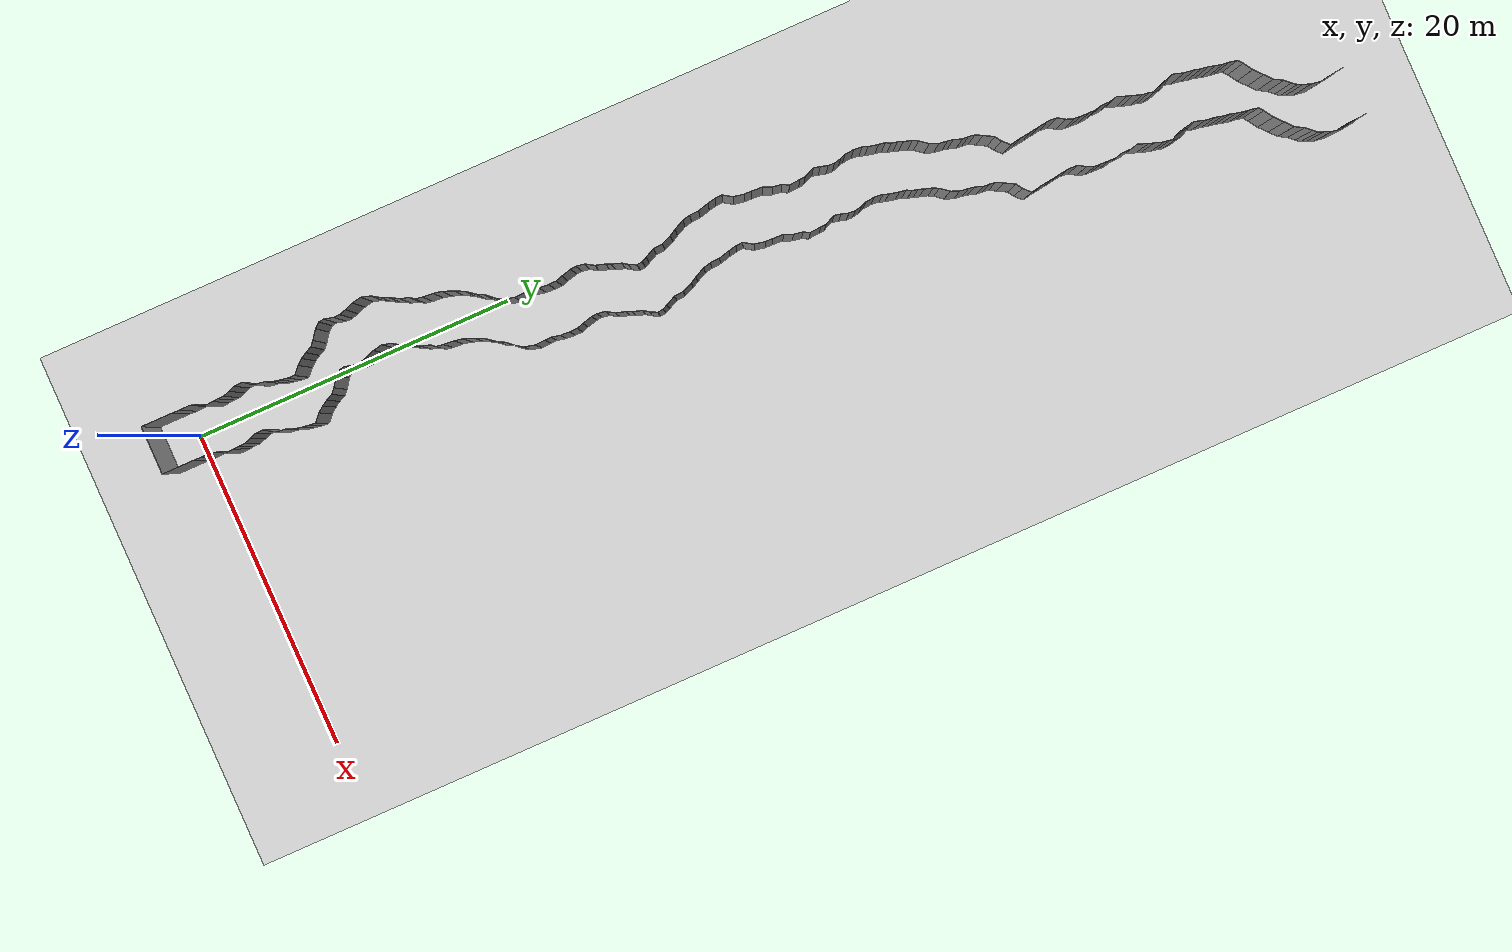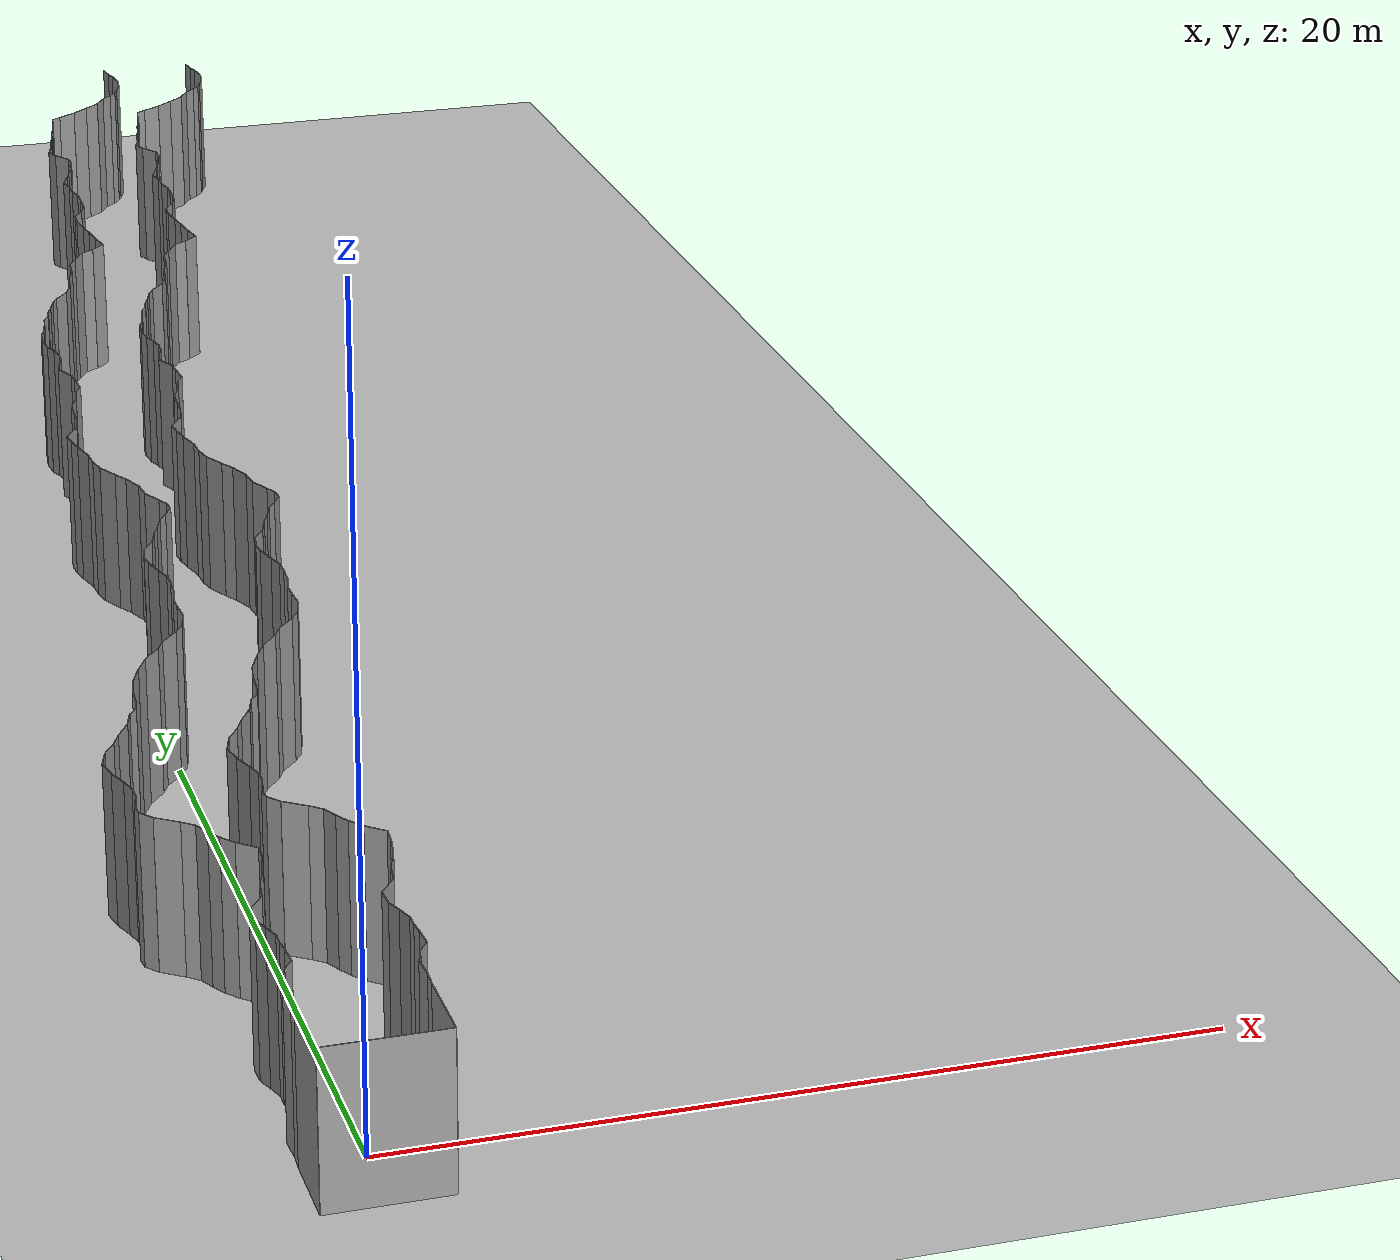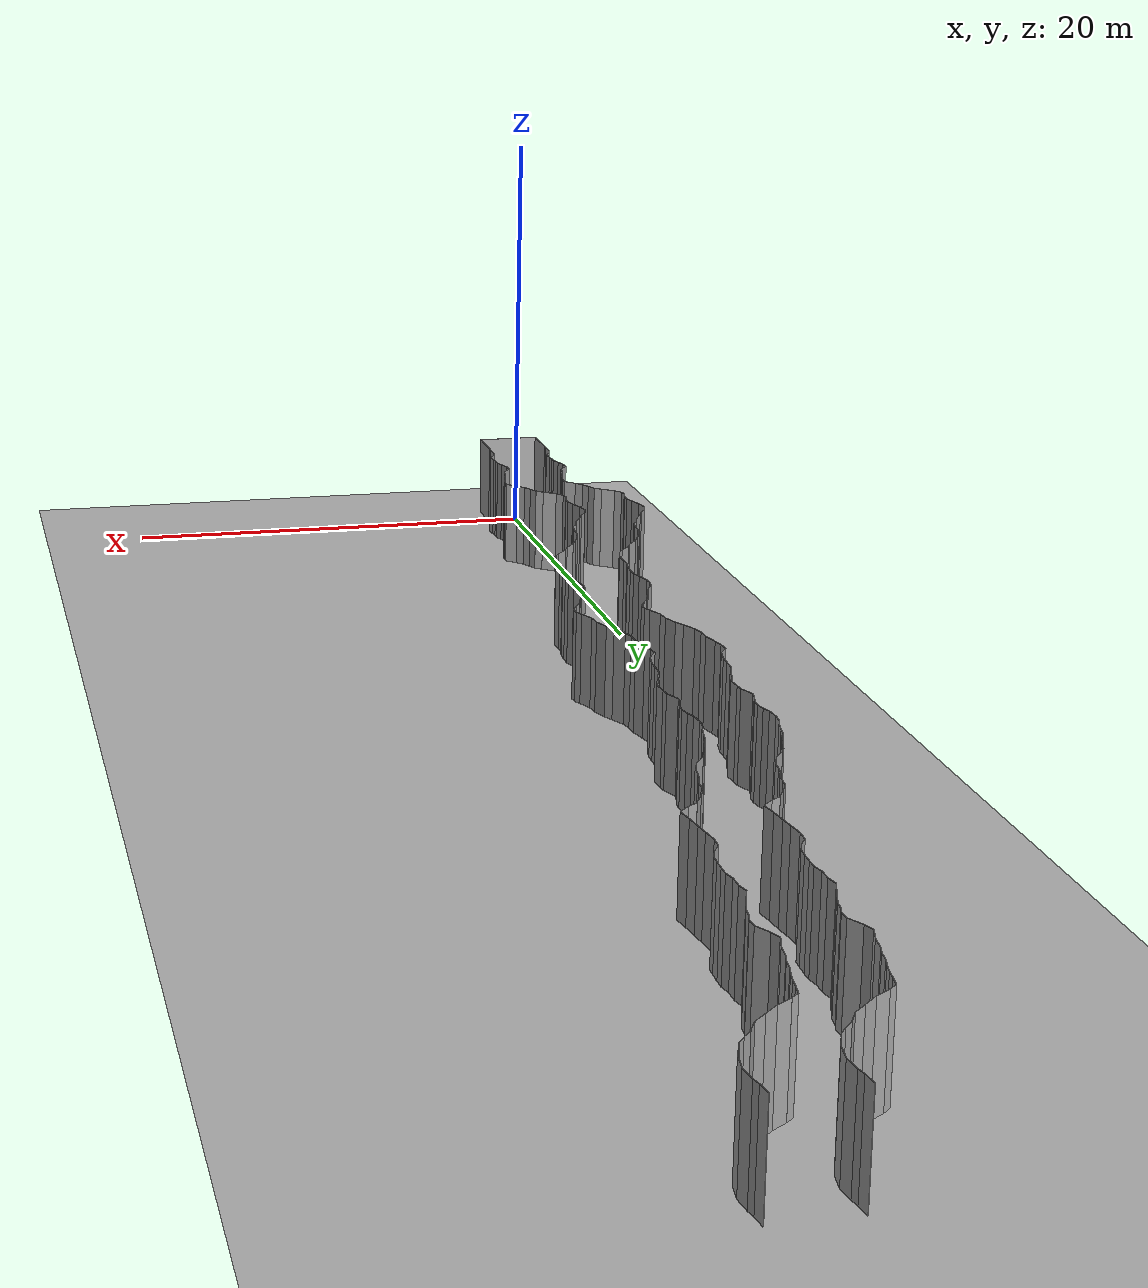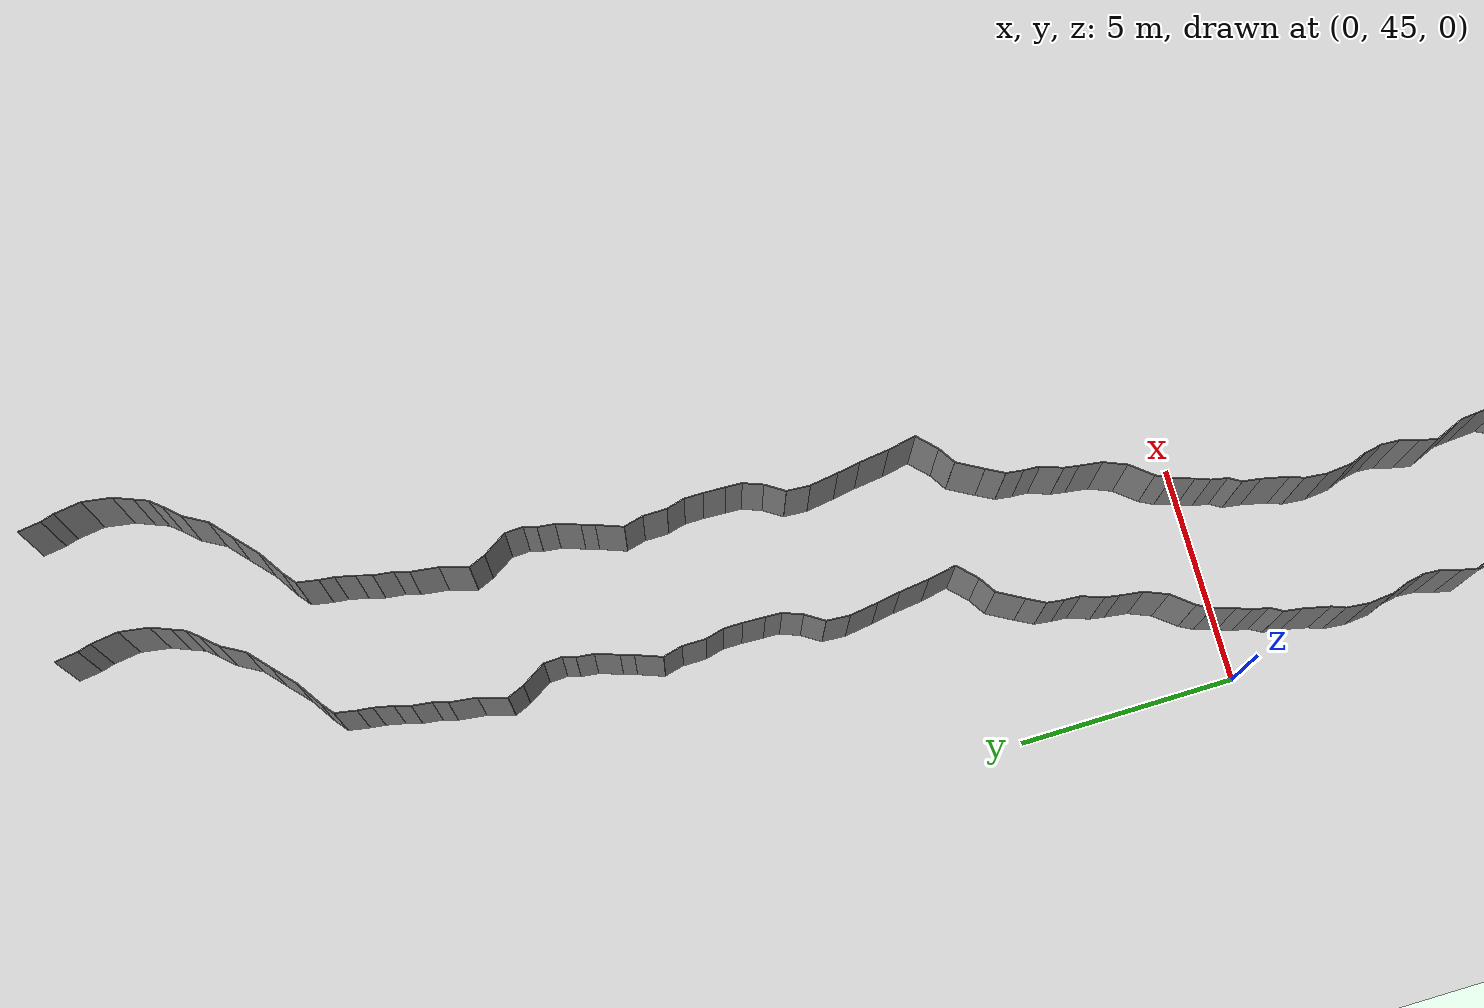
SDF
<sdf version="1.6">
 <world name="default">
  <light name="sun" type="directional">
   <pose>0 0 10 0 -0 0</pose>
   <diffuse>0.8 0.8 0.8 1</diffuse>
   <specular>0.2 0.2 0.2 1</specular>
   <attenuation>
    <range>1000</range>
    <constant>0.9</constant>
    <linear>0.01</linear>
    <quadratic>0.001</quadratic>
   </attenuation>
   <direction>-0.5 0.1 -0.9</direction>
  </light>
  <model name="ground_plane">
   <static>1</static>
   <link name="link">
    <collision name="collision">
     <geometry><plane><normal>0 0 1</normal><size>200 200</size></plane></geometry>
     <surface><friction><ode><mu>100</mu><mu2>50</mu2></ode></friction></surface>
    </collision>
    <visual name="visual">
     <cast_shadows>0</cast_shadows>
     <geometry><plane><normal>0 0 1</normal><size>200 200</size></plane></geometry>
     <material>
      <script><uri>file://media/materials/scripts/gazebo.material</uri><name>Gazebo/Grey</name></script>
     </material>
    </visual>
   </link>
   <pose>0 100 0 0 -0 0</pose>
  </model>
  <gravity>0 0 -9.8</gravity>
  <magnetic_field>6e-06 2.3e-05 -4.2e-05</magnetic_field>
  <atmosphere type="adiabatic"/>
  <physics default="0" name="default_physics" type="ode">
   <max_step_size>0.001</max_step_size>
   <real_time_factor>1</real_time_factor>
   <real_time_update_rate>1000</real_time_update_rate>
  </physics>
  <scene><ambient>0.4 0.4 0.4 1</ambient><background>0.7 0.7 0.7 1</background><shadows>1</shadows></scene>
  <spherical_coordinates>
   <surface_model>EARTH_WGS84</surface_model>
   <latitude_deg>0</latitude_deg>
   <longitude_deg>0</longitude_deg>
   <elevation>0</elevation>
   <heading_deg>0</heading_deg>
  </spherical_coordinates>
  <model name="wall_back">
   <static>1</static>
   <pose>0.0 -2 2 0.0 0 0.0</pose>
   <link name="link">
    <collision name="collision"><geometry><box><size>3 0.02 4</size></box></geometry></collision>
    <visual name="visual">
     <material>
      <script><name>Gazebo/Grey</name><uri>file://media/materials/scripts/gazebo.material</uri></script>
     </material>
     <geometry><box><size>3 0.02 4</size></box></geometry>
    </visual>
   </link>
  </model>
  <model name="wall_left">
   <static>1</static>
   <pose>1.5 -1 2 0 0 0.00</pose>
   <link name="link">
    <collision name="collision"><geometry><box><size>0.02 2 4</size></box></geometry></collision>
    <visual name="visual">
     <material>
      <script><name>Gazebo/Grey</name><uri>file://media/materials/scripts/gazebo.material</uri></script>
     </material>
     <geometry><box><size>0.02 2 4</size></box></geometry>
    </visual>
   </link>
  </model>
  <model name="wall_right">
   <static>1</static>
   <pose>-1.5 -1 2 0 0 0.00</pose>
   <link name="link">
    <collision name="collision"><geometry><box><size>0.02 2 4</size></box></geometry></collision>
    <visual name="visual">
     <material>
      <script><name>Gazebo/Grey</name><uri>file://media/materials/scripts/gazebo.material</uri></script>
     </material>
     <geometry><box><size>0.02 2 4</size></box></geometry>
    </visual>
   </link>
  </model>
  <model name="wall_0">
   <static>1</static>
   <pose>-1.4882764382496583 0.2142436278795868 2 0 0 -0.05466618233456685</pose>
   <link name="link">
    <collision name="collision"><geometry><box><size>0.02 0.429128297772 4</size></box></geometry></collision>
    <visual name="visual">
     <material>
      <script><name>Gazebo/Grey</name><uri>file://media/materials/scripts/gazebo.material</uri></script>
     </material>
     <geometry><box><size>0.02 0.429128297772 4</size></box></geometry>
    </visual>
   </link>
  </model>
  <model name="wall_1">
   <static>1</static>
   <pose>1.5117235617503417 0.2142436278795868 2 0 0 -0.05466618233456685</pose>
   <link name="link">
    <collision name="collision"><geometry><box><size>0.02 0.429128297772 4</size></box></geometry></collision>
    <visual name="visual">
     <material>
      <script><name>Gazebo/Grey</name><uri>file://media/materials/scripts/gazebo.material</uri></script>
     </material>
     <geometry><box><size>0.02 0.429128297772 4</size></box></geometry>
    </visual>
   </link>
  </model>
  <model name="wall_2">
   <static>1</static>
   <pose>-1.4906252148911652 0.7485332617188468 2 0 0 0.04394143271486499</pose>
   <link name="link">
    <collision name="collision"><geometry><box><size>0.02 0.640710470146 4</size></box></geometry></collision>
    <visual name="visual">
     <material>
      <script><name>Gazebo/Grey</name><uri>file://media/materials/scripts/gazebo.material</uri></script>
     </material>
     <geometry><box><size>0.02 0.640710470146 4</size></box></geometry>
    </visual>
   </link>
  </model>
  <model name="wall_3">
   <static>1</static>
   <pose>1.5093747851088348 0.7485332617188468 2 0 0 0.04394143271486499</pose>
   <link name="link">
    <collision name="collision"><geometry><box><size>0.02 0.640710470146 4</size></box></geometry></collision>
    <visual name="visual">
     <material>
      <script><name>Gazebo/Grey</name><uri>file://media/materials/scripts/gazebo.material</uri></script>
     </material>
     <geometry><box><size>0.02 0.640710470146 4</size></box></geometry>
    </visual>
   </link>
  </model>
  <model name="wall_4">
   <static>1</static>
   <pose>-1.4351299684521113 1.28706230178726 2 0 0 -0.3082616422023971</pose>
   <link name="link">
    <collision name="collision"><geometry><box><size>0.02 0.458582533695 4</size></box></geometry></collision>
    <visual name="visual">
     <material>
      <script><name>Gazebo/Grey</name><uri>file://media/materials/scripts/gazebo.material</uri></script>
     </material>
     <geometry><box><size>0.02 0.458582533695 4</size></box></geometry>
    </visual>
   </link>
  </model>
  <model name="wall_5">
   <static>1</static>
   <pose>1.5648700315478887 1.28706230178726 2 0 0 -0.3082616422023971</pose>
   <link name="link">
    <collision name="collision"><geometry><box><size>0.02 0.458582533695 4</size></box></geometry></collision>
    <visual name="visual">
     <material>
      <script><name>Gazebo/Grey</name><uri>file://media/materials/scripts/gazebo.material</uri></script>
     </material>
     <geometry><box><size>0.02 0.458582533695 4</size></box></geometry>
    </visual>
   </link>
  </model>
  <model name="wall_6">
   <static>1</static>
   <pose>-1.246430500729539 1.6787287137718458 2 0 0 -0.6025551399527813</pose>
   <link name="link">
    <collision name="collision"><geometry><box><size>0.02 0.420404033729 4</size></box></geometry></collision>
    <visual name="visual">
     <material>
      <script><name>Gazebo/Grey</name><uri>file://media/materials/scripts/gazebo.material</uri></script>
     </material>
     <geometry><box><size>0.02 0.420404033729 4</size></box></geometry>
    </visual>
   </link>
  </model>
  <model name="wall_7">
   <static>1</static>
   <pose>1.753569499270461 1.6787287137718458 2 0 0 -0.6025551399527813</pose>
   <link name="link">
    <collision name="collision"><geometry><box><size>0.02 0.420404033729 4</size></box></geometry></collision>
    <visual name="visual">
     <material>
      <script><name>Gazebo/Grey</name><uri>file://media/materials/scripts/gazebo.material</uri></script>
     </material>
     <geometry><box><size>0.02 0.420404033729 4</size></box></geometry>
    </visual>
   </link>
  </model>
  <model name="wall_8">
   <static>1</static>
   <pose>-1.1423110355689778 2.126357916920006 2 0 0 0.054646381465795514</pose>
   <link name="link">
    <collision name="collision"><geometry><box><size>0.02 0.549712229064 4</size></box></geometry></collision>
    <visual name="visual">
     <material>
      <script><name>Gazebo/Grey</name><uri>file://media/materials/scripts/gazebo.material</uri></script>
     </material>
     <geometry><box><size>0.02 0.549712229064 4</size></box></geometry>
    </visual>
   </link>
  </model>
  <model name="wall_9">
   <static>1</static>
   <pose>1.8576889644310222 2.126357916920006 2 0 0 0.054646381465795514</pose>
   <link name="link">
    <collision name="collision"><geometry><box><size>0.02 0.549712229064 4</size></box></geometry></collision>
    <visual name="visual">
     <material>
      <script><name>Gazebo/Grey</name><uri>file://media/materials/scripts/gazebo.material</uri></script>
     </material>
     <geometry><box><size>0.02 0.549712229064 4</size></box></geometry>
    </visual>
   </link>
  </model>
  <model name="wall_10">
   <static>1</static>
   <pose>-1.174572083154149 2.5600124033881193 2 0 0 0.10791885154700406</pose>
   <link name="link">
    <collision name="collision"><geometry><box><size>0.02 0.320280583436 4</size></box></geometry></collision>
    <visual name="visual">
     <material>
      <script><name>Gazebo/Grey</name><uri>file://media/materials/scripts/gazebo.material</uri></script>
     </material>
     <geometry><box><size>0.02 0.320280583436 4</size></box></geometry>
    </visual>
   </link>
  </model>
  <model name="wall_11">
   <static>1</static>
   <pose>1.825427916845851 2.5600124033881193 2 0 0 0.10791885154700406</pose>
   <link name="link">
    <collision name="collision"><geometry><box><size>0.02 0.320280583436 4</size></box></geometry></collision>
    <visual name="visual">
     <material>
      <script><name>Gazebo/Grey</name><uri>file://media/materials/scripts/gazebo.material</uri></script>
     </material>
     <geometry><box><size>0.02 0.320280583436 4</size></box></geometry>
    </visual>
   </link>
  </model>
  <model name="wall_12">
   <static>1</static>
   <pose>-1.1913653444094687 2.899216656177083 2 0 0 -0.0025298821110752733</pose>
   <link name="link">
    <collision name="collision"><geometry><box><size>0.02 0.359992335216 4</size></box></geometry></collision>
    <visual name="visual">
     <material>
      <script><name>Gazebo/Grey</name><uri>file://media/materials/scripts/gazebo.material</uri></script>
     </material>
     <geometry><box><size>0.02 0.359992335216 4</size></box></geometry>
    </visual>
   </link>
  </model>
  <model name="wall_13">
   <static>1</static>
   <pose>1.8086346555905313 2.899216656177083 2 0 0 -0.0025298821110752733</pose>
   <link name="link">
    <collision name="collision"><geometry><box><size>0.02 0.359992335216 4</size></box></geometry></collision>
    <visual name="visual">
     <material>
      <script><name>Gazebo/Grey</name><uri>file://media/materials/scripts/gazebo.material</uri></script>
     </material>
     <geometry><box><size>0.02 0.359992335216 4</size></box></geometry>
    </visual>
   </link>
  </model>
  <model name="wall_14">
   <static>1</static>
   <pose>-1.2577946661947295 3.281178483480198 2 0 0 0.3198002047015978</pose>
   <link name="link">
    <collision name="collision"><geometry><box><size>0.02 0.425506390902 4</size></box></geometry></collision>
    <visual name="visual">
     <material>
      <script><name>Gazebo/Grey</name><uri>file://media/materials/scripts/gazebo.material</uri></script>
     </material>
     <geometry><box><size>0.02 0.425506390902 4</size></box></geometry>
    </visual>
   </link>
  </model>
  <model name="wall_15">
   <static>1</static>
   <pose>1.7422053338052705 3.281178483480198 2 0 0 0.3198002047015978</pose>
   <link name="link">
    <collision name="collision"><geometry><box><size>0.02 0.425506390902 4</size></box></geometry></collision>
    <visual name="visual">
     <material>
      <script><name>Gazebo/Grey</name><uri>file://media/materials/scripts/gazebo.material</uri></script>
     </material>
     <geometry><box><size>0.02 0.425506390902 4</size></box></geometry>
    </visual>
   </link>
  </model>
  <model name="wall_16">
   <static>1</static>
   <pose>-1.3988093052747013 3.678838255260796 2 0 0 0.3621035368704639</pose>
   <link name="link">
    <collision name="collision"><geometry><box><size>0.02 0.418526985288 4</size></box></geometry></collision>
    <visual name="visual">
     <material>
      <script><name>Gazebo/Grey</name><uri>file://media/materials/scripts/gazebo.material</uri></script>
     </material>
     <geometry><box><size>0.02 0.418526985288 4</size></box></geometry>
    </visual>
   </link>
  </model>
  <model name="wall_17">
   <static>1</static>
   <pose>1.6011906947252987 3.678838255260796 2 0 0 0.3621035368704639</pose>
   <link name="link">
    <collision name="collision"><geometry><box><size>0.02 0.418526985288 4</size></box></geometry></collision>
    <visual name="visual">
     <material>
      <script><name>Gazebo/Grey</name><uri>file://media/materials/scripts/gazebo.material</uri></script>
     </material>
     <geometry><box><size>0.02 0.418526985288 4</size></box></geometry>
    </visual>
   </link>
  </model>
  <model name="wall_18">
   <static>1</static>
   <pose>-1.4835313058364274 4.134646809943204 2 0 0 0.04069816215118509</pose>
   <link name="link">
    <collision name="collision"><geometry><box><size>0.02 0.520661173779 4</size></box></geometry></collision>
    <visual name="visual">
     <material>
      <script><name>Gazebo/Grey</name><uri>file://media/materials/scripts/gazebo.material</uri></script>
     </material>
     <geometry><box><size>0.02 0.520661173779 4</size></box></geometry>
    </visual>
   </link>
  </model>
  <model name="wall_19">
   <static>1</static>
   <pose>1.5164686941635726 4.134646809943204 2 0 0 0.04069816215118509</pose>
   <link name="link">
    <collision name="collision"><geometry><box><size>0.02 0.520661173779 4</size></box></geometry></collision>
    <visual name="visual">
     <material>
      <script><name>Gazebo/Grey</name><uri>file://media/materials/scripts/gazebo.material</uri></script>
     </material>
     <geometry><box><size>0.02 0.520661173779 4</size></box></geometry>
    </visual>
   </link>
  </model>
  <model name="wall_20">
   <static>1</static>
   <pose>-1.291361722227489 4.677735634371101 2 0 0 -0.6217396278905083</pose>
   <link name="link">
    <collision name="collision"><geometry><box><size>0.02 0.696236901057 4</size></box></geometry></collision>
    <visual name="visual">
     <material>
      <script><name>Gazebo/Grey</name><uri>file://media/materials/scripts/gazebo.material</uri></script>
     </material>
     <geometry><box><size>0.02 0.696236901057 4</size></box></geometry>
    </visual>
   </link>
  </model>
  <model name="wall_21">
   <static>1</static>
   <pose>1.708638277772511 4.677735634371101 2 0 0 -0.6217396278905083</pose>
   <link name="link">
    <collision name="collision"><geometry><box><size>0.02 0.696236901057 4</size></box></geometry></collision>
    <visual name="visual">
     <material>
      <script><name>Gazebo/Grey</name><uri>file://media/materials/scripts/gazebo.material</uri></script>
     </material>
     <geometry><box><size>0.02 0.696236901057 4</size></box></geometry>
    </visual>
   </link>
  </model>
  <model name="wall_22">
   <static>1</static>
   <pose>-1.0434823716316737 5.284158940186959 2 0 0 -0.13859493508668264</pose>
   <link name="link">
    <collision name="collision"><geometry><box><size>0.02 0.653162115459 4</size></box></geometry></collision>
    <visual name="visual">
     <material>
      <script><name>Gazebo/Grey</name><uri>file://media/materials/scripts/gazebo.material</uri></script>
     </material>
     <geometry><box><size>0.02 0.653162115459 4</size></box></geometry>
    </visual>
   </link>
  </model>
  <model name="wall_23">
   <static>1</static>
   <pose>1.9565176283683263 5.284158940186959 2 0 0 -0.13859493508668264</pose>
   <link name="link">
    <collision name="collision"><geometry><box><size>0.02 0.653162115459 4</size></box></geometry></collision>
    <visual name="visual">
     <material>
      <script><name>Gazebo/Grey</name><uri>file://media/materials/scripts/gazebo.material</uri></script>
     </material>
     <geometry><box><size>0.02 0.653162115459 4</size></box></geometry>
    </visual>
   </link>
  </model>
  <model name="wall_24">
   <static>1</static>
   <pose>-0.9033312365255437 5.846805654554143 2 0 0 -0.37817795014542205</pose>
   <link name="link">
    <collision name="collision"><geometry><box><size>0.02 0.514768523805 4</size></box></geometry></collision>
    <visual name="visual">
     <material>
      <script><name>Gazebo/Grey</name><uri>file://media/materials/scripts/gazebo.material</uri></script>
     </material>
     <geometry><box><size>0.02 0.514768523805 4</size></box></geometry>
    </visual>
   </link>
  </model>
  <model name="wall_25">
   <static>1</static>
   <pose>2.0966687634744563 5.846805654554143 2 0 0 -0.37817795014542205</pose>
   <link name="link">
    <collision name="collision"><geometry><box><size>0.02 0.514768523805 4</size></box></geometry></collision>
    <visual name="visual">
     <material>
      <script><name>Gazebo/Grey</name><uri>file://media/materials/scripts/gazebo.material</uri></script>
     </material>
     <geometry><box><size>0.02 0.514768523805 4</size></box></geometry>
    </visual>
   </link>
  </model>
  <model name="wall_26">
   <static>1</static>
   <pose>-0.7707080896181243 6.274854521695362 2 0 0 -0.19647584731231973</pose>
   <link name="link">
    <collision name="collision"><geometry><box><size>0.02 0.385112629372 4</size></box></geometry></collision>
    <visual name="visual">
     <material>
      <script><name>Gazebo/Grey</name><uri>file://media/materials/scripts/gazebo.material</uri></script>
     </material>
     <geometry><box><size>0.02 0.385112629372 4</size></box></geometry>
    </visual>
   </link>
  </model>
  <model name="wall_27">
   <static>1</static>
   <pose>2.2292919103818756 6.274854521695362 2 0 0 -0.19647584731231973</pose>
   <link name="link">
    <collision name="collision"><geometry><box><size>0.02 0.385112629372 4</size></box></geometry></collision>
    <visual name="visual">
     <material>
      <script><name>Gazebo/Grey</name><uri>file://media/materials/scripts/gazebo.material</uri></script>
     </material>
     <geometry><box><size>0.02 0.385112629372 4</size></box></geometry>
    </visual>
   </link>
  </model>
  <model name="wall_28">
   <static>1</static>
   <pose>-0.6978907470432615 6.674351680986191 2 0 0 -0.16570305118177842</pose>
   <link name="link">
    <collision name="collision"><geometry><box><size>0.02 0.427141729736 4</size></box></geometry></collision>
    <visual name="visual">
     <material>
      <script><name>Gazebo/Grey</name><uri>file://media/materials/scripts/gazebo.material</uri></script>
     </material>
     <geometry><box><size>0.02 0.427141729736 4</size></box></geometry>
    </visual>
   </link>
  </model>
  <model name="wall_29">
   <static>1</static>
   <pose>2.3021092529567384 6.674351680986191 2 0 0 -0.16570305118177842</pose>
   <link name="link">
    <collision name="collision"><geometry><box><size>0.02 0.427141729736 4</size></box></geometry></collision>
    <visual name="visual">
     <material>
      <script><name>Gazebo/Grey</name><uri>file://media/materials/scripts/gazebo.material</uri></script>
     </material>
     <geometry><box><size>0.02 0.427141729736 4</size></box></geometry>
    </visual>
   </link>
  </model>
  <model name="wall_30">
   <static>1</static>
   <pose>-0.6468937416393523 7.1045311742987955 2 0 0 -0.07170803825115375</pose>
   <link name="link">
    <collision name="collision"><geometry><box><size>0.02 0.440199250392 4</size></box></geometry></collision>
    <visual name="visual">
     <material>
      <script><name>Gazebo/Grey</name><uri>file://media/materials/scripts/gazebo.material</uri></script>
     </material>
     <geometry><box><size>0.02 0.440199250392 4</size></box></geometry>
    </visual>
   </link>
  </model>
  <model name="wall_31">
   <static>1</static>
   <pose>2.353106258360648 7.1045311742987955 2 0 0 -0.07170803825115375</pose>
   <link name="link">
    <collision name="collision"><geometry><box><size>0.02 0.440199250392 4</size></box></geometry></collision>
    <visual name="visual">
     <material>
      <script><name>Gazebo/Grey</name><uri>file://media/materials/scripts/gazebo.material</uri></script>
     </material>
     <geometry><box><size>0.02 0.440199250392 4</size></box></geometry>
    </visual>
   </link>
  </model>
  <model name="wall_32">
   <static>1</static>
   <pose>-0.8582554405534828 7.529582275134427 2 0 0 0.8353140544356459</pose>
   <link name="link">
    <collision name="collision"><geometry><box><size>0.02 0.612619998373 4</size></box></geometry></collision>
    <visual name="visual">
     <material>
      <script><name>Gazebo/Grey</name><uri>file://media/materials/scripts/gazebo.material</uri></script>
     </material>
     <geometry><box><size>0.02 0.612619998373 4</size></box></geometry>
    </visual>
   </link>
  </model>
  <model name="wall_33">
   <static>1</static>
   <pose>2.141744559446517 7.529582275134427 2 0 0 0.8353140544356459</pose>
   <link name="link">
    <collision name="collision"><geometry><box><size>0.02 0.612619998373 4</size></box></geometry></collision>
    <visual name="visual">
     <material>
      <script><name>Gazebo/Grey</name><uri>file://media/materials/scripts/gazebo.material</uri></script>
     </material>
     <geometry><box><size>0.02 0.612619998373 4</size></box></geometry>
    </visual>
   </link>
  </model>
  <model name="wall_34">
   <static>1</static>
   <pose>-1.2252234323262905 7.91197370236085 2 0 0 0.6689831428733833</pose>
   <link name="link">
    <collision name="collision"><geometry><box><size>0.02 0.450949585367 4</size></box></geometry></collision>
    <visual name="visual">
     <material>
      <script><name>Gazebo/Grey</name><uri>file://media/materials/scripts/gazebo.material</uri></script>
     </material>
     <geometry><box><size>0.02 0.450949585367 4</size></box></geometry>
    </visual>
   </link>
  </model>
  <model name="wall_35">
   <static>1</static>
   <pose>1.7747765676737095 7.91197370236085 2 0 0 0.6689831428733833</pose>
   <link name="link">
    <collision name="collision"><geometry><box><size>0.02 0.450949585367 4</size></box></geometry></collision>
    <visual name="visual">
     <material>
      <script><name>Gazebo/Grey</name><uri>file://media/materials/scripts/gazebo.material</uri></script>
     </material>
     <geometry><box><size>0.02 0.450949585367 4</size></box></geometry>
    </visual>
   </link>
  </model>
  <model name="wall_36">
   <static>1</static>
   <pose>-1.4694159097178903 8.266232441602584 2 0 0 0.5317734631163602</pose>
   <link name="link">
    <collision name="collision"><geometry><box><size>0.02 0.411608165571 4</size></box></geometry></collision>
    <visual name="visual">
     <material>
      <script><name>Gazebo/Grey</name><uri>file://media/materials/scripts/gazebo.material</uri></script>
     </material>
     <geometry><box><size>0.02 0.411608165571 4</size></box></geometry>
    </visual>
   </link>
  </model>
  <model name="wall_37">
   <static>1</static>
   <pose>1.5305840902821097 8.266232441602584 2 0 0 0.5317734631163602</pose>
   <link name="link">
    <collision name="collision"><geometry><box><size>0.02 0.411608165571 4</size></box></geometry></collision>
    <visual name="visual">
     <material>
      <script><name>Gazebo/Grey</name><uri>file://media/materials/scripts/gazebo.material</uri></script>
     </material>
     <geometry><box><size>0.02 0.411608165571 4</size></box></geometry>
    </visual>
   </link>
  </model>
  <model name="wall_38">
   <static>1</static>
   <pose>-1.6702580753962393 8.64240468940797 2 0 0 0.45187911080128523</pose>
   <link name="link">
    <collision name="collision"><geometry><box><size>0.02 0.441933299922 4</size></box></geometry></collision>
    <visual name="visual">
     <material>
      <script><name>Gazebo/Grey</name><uri>file://media/materials/scripts/gazebo.material</uri></script>
     </material>
     <geometry><box><size>0.02 0.441933299922 4</size></box></geometry>
    </visual>
   </link>
  </model>
  <model name="wall_39">
   <static>1</static>
   <pose>1.3297419246037607 8.64240468940797 2 0 0 0.45187911080128523</pose>
   <link name="link">
    <collision name="collision"><geometry><box><size>0.02 0.441933299922 4</size></box></geometry></collision>
    <visual name="visual">
     <material>
      <script><name>Gazebo/Grey</name><uri>file://media/materials/scripts/gazebo.material</uri></script>
     </material>
     <geometry><box><size>0.02 0.441933299922 4</size></box></geometry>
    </visual>
   </link>
  </model>
  <model name="wall_40">
   <static>1</static>
   <pose>-1.9162545087971874 8.970234238321153 2 0 0 0.8587468627552496</pose>
   <link name="link">
    <collision name="collision"><geometry><box><size>0.02 0.394993469345 4</size></box></geometry></collision>
    <visual name="visual">
     <material>
      <script><name>Gazebo/Grey</name><uri>file://media/materials/scripts/gazebo.material</uri></script>
     </material>
     <geometry><box><size>0.02 0.394993469345 4</size></box></geometry>
    </visual>
   </link>
  </model>
  <model name="wall_41">
   <static>1</static>
   <pose>1.0837454912028126 8.970234238321153 2 0 0 0.8587468627552496</pose>
   <link name="link">
    <collision name="collision"><geometry><box><size>0.02 0.394993469345 4</size></box></geometry></collision>
    <visual name="visual">
     <material>
      <script><name>Gazebo/Grey</name><uri>file://media/materials/scripts/gazebo.material</uri></script>
     </material>
     <geometry><box><size>0.02 0.394993469345 4</size></box></geometry>
    </visual>
   </link>
  </model>
  <model name="wall_42">
   <static>1</static>
   <pose>-2.3441185255960963 9.305867519616344 2 0 0 0.9323126875459886</pose>
   <link name="link">
    <collision name="collision"><geometry><box><size>0.02 0.693285271336 4</size></box></geometry></collision>
    <visual name="visual">
     <material>
      <script><name>Gazebo/Grey</name><uri>file://media/materials/scripts/gazebo.material</uri></script>
     </material>
     <geometry><box><size>0.02 0.693285271336 4</size></box></geometry>
    </visual>
   </link>
  </model>
  <model name="wall_43">
   <static>1</static>
   <pose>0.6558814744039037 9.305867519616344 2 0 0 0.9323126875459886</pose>
   <link name="link">
    <collision name="collision"><geometry><box><size>0.02 0.693285271336 4</size></box></geometry></collision>
    <visual name="visual">
     <material>
      <script><name>Gazebo/Grey</name><uri>file://media/materials/scripts/gazebo.material</uri></script>
     </material>
     <geometry><box><size>0.02 0.693285271336 4</size></box></geometry>
    </visual>
   </link>
  </model>
  <model name="wall_44">
   <static>1</static>
   <pose>-2.7574374389931626 9.680984901777562 2 0 0 0.6752620178453725</pose>
   <link name="link">
    <collision name="collision"><geometry><box><size>0.02 0.431816791613 4</size></box></geometry></collision>
    <visual name="visual">
     <material>
      <script><name>Gazebo/Grey</name><uri>file://media/materials/scripts/gazebo.material</uri></script>
     </material>
     <geometry><box><size>0.02 0.431816791613 4</size></box></geometry>
    </visual>
   </link>
  </model>
  <model name="wall_45">
   <static>1</static>
   <pose>0.24256256100683737 9.680984901777562 2 0 0 0.6752620178453725</pose>
   <link name="link">
    <collision name="collision"><geometry><box><size>0.02 0.431816791613 4</size></box></geometry></collision>
    <visual name="visual">
     <material>
      <script><name>Gazebo/Grey</name><uri>file://media/materials/scripts/gazebo.material</uri></script>
     </material>
     <geometry><box><size>0.02 0.431816791613 4</size></box></geometry>
    </visual>
   </link>
  </model>
  <model name="wall_46">
   <static>1</static>
   <pose>-2.912614911732244 10.011275955388916 2 0 0 0.12430679334028681</pose>
   <link name="link">
    <collision name="collision"><geometry><box><size>0.02 0.326046271739 4</size></box></geometry></collision>
    <visual name="visual">
     <material>
      <script><name>Gazebo/Grey</name><uri>file://media/materials/scripts/gazebo.material</uri></script>
     </material>
     <geometry><box><size>0.02 0.326046271739 4</size></box></geometry>
    </visual>
   </link>
  </model>
  <model name="wall_47">
   <static>1</static>
   <pose>0.08738508826775604 10.011275955388916 2 0 0 0.12430679334028681</pose>
   <link name="link">
    <collision name="collision"><geometry><box><size>0.02 0.326046271739 4</size></box></geometry></collision>
    <visual name="visual">
     <material>
      <script><name>Gazebo/Grey</name><uri>file://media/materials/scripts/gazebo.material</uri></script>
     </material>
     <geometry><box><size>0.02 0.326046271739 4</size></box></geometry>
    </visual>
   </link>
  </model>
  <model name="wall_48">
   <static>1</static>
   <pose>-2.8625477616231083 10.453642308325819 2 0 0 -0.2454133209354726</pose>
   <link name="link">
    <collision name="collision"><geometry><box><size>0.02 0.578536964427 4</size></box></geometry></collision>
    <visual name="visual">
     <material>
      <script><name>Gazebo/Grey</name><uri>file://media/materials/scripts/gazebo.material</uri></script>
     </material>
     <geometry><box><size>0.02 0.578536964427 4</size></box></geometry>
    </visual>
   </link>
  </model>
  <model name="wall_49">
   <static>1</static>
   <pose>0.1374522383768917 10.453642308325819 2 0 0 -0.2454133209354726</pose>
   <link name="link">
    <collision name="collision"><geometry><box><size>0.02 0.578536964427 4</size></box></geometry></collision>
    <visual name="visual">
     <material>
      <script><name>Gazebo/Grey</name><uri>file://media/materials/scripts/gazebo.material</uri></script>
     </material>
     <geometry><box><size>0.02 0.578536964427 4</size></box></geometry>
    </visual>
   </link>
  </model>
  <model name="wall_50">
   <static>1</static>
   <pose>-2.794264964281337 10.93220077968322 2 0 0 0.010088128646324556</pose>
   <link name="link">
    <collision name="collision"><geometry><box><size>0.02 0.395934835046 4</size></box></geometry></collision>
    <visual name="visual">
     <material>
      <script><name>Gazebo/Grey</name><uri>file://media/materials/scripts/gazebo.material</uri></script>
     </material>
     <geometry><box><size>0.02 0.395934835046 4</size></box></geometry>
    </visual>
   </link>
  </model>
  <model name="wall_51">
   <static>1</static>
   <pose>0.20573503571866292 10.93220077968322 2 0 0 0.010088128646324556</pose>
   <link name="link">
    <collision name="collision"><geometry><box><size>0.02 0.395934835046 4</size></box></geometry></collision>
    <visual name="visual">
     <material>
      <script><name>Gazebo/Grey</name><uri>file://media/materials/scripts/gazebo.material</uri></script>
     </material>
     <geometry><box><size>0.02 0.395934835046 4</size></box></geometry>
    </visual>
   </link>
  </model>
  <model name="wall_52">
   <static>1</static>
   <pose>-2.857294968850871 11.33792524997233 2 0 0 0.28571889998937416</pose>
   <link name="link">
    <collision name="collision"><geometry><box><size>0.02 0.433092118628 4</size></box></geometry></collision>
    <visual name="visual">
     <material>
      <script><name>Gazebo/Grey</name><uri>file://media/materials/scripts/gazebo.material</uri></script>
     </material>
     <geometry><box><size>0.02 0.433092118628 4</size></box></geometry>
    </visual>
   </link>
  </model>
  <model name="wall_53">
   <static>1</static>
   <pose>0.1427050311491289 11.33792524997233 2 0 0 0.28571889998937416</pose>
   <link name="link">
    <collision name="collision"><geometry><box><size>0.02 0.433092118628 4</size></box></geometry></collision>
    <visual name="visual">
     <material>
      <script><name>Gazebo/Grey</name><uri>file://media/materials/scripts/gazebo.material</uri></script>
     </material>
     <geometry><box><size>0.02 0.433092118628 4</size></box></geometry>
    </visual>
   </link>
  </model>
  <model name="wall_54">
   <static>1</static>
   <pose>-3.0135029106652866 11.809593357492517 2 0 0 0.3461279866709444</pose>
   <link name="link">
    <collision name="collision"><geometry><box><size>0.02 0.561077581507 4</size></box></geometry></collision>
    <visual name="visual">
     <material>
      <script><name>Gazebo/Grey</name><uri>file://media/materials/scripts/gazebo.material</uri></script>
     </material>
     <geometry><box><size>0.02 0.561077581507 4</size></box></geometry>
    </visual>
   </link>
  </model>
  <model name="wall_55">
   <static>1</static>
   <pose>-0.013502910665286638 11.809593357492517 2 0 0 0.3461279866709444</pose>
   <link name="link">
    <collision name="collision"><geometry><box><size>0.02 0.561077581507 4</size></box></geometry></collision>
    <visual name="visual">
     <material>
      <script><name>Gazebo/Grey</name><uri>file://media/materials/scripts/gazebo.material</uri></script>
     </material>
     <geometry><box><size>0.02 0.561077581507 4</size></box></geometry>
    </visual>
   </link>
  </model>
  <model name="wall_56">
   <static>1</static>
   <pose>-3.1654130749152403 12.362162091811154 2 0 0 0.19406770105616922</pose>
   <link name="link">
    <collision name="collision"><geometry><box><size>0.02 0.588380651598 4</size></box></geometry></collision>
    <visual name="visual">
     <material>
      <script><name>Gazebo/Grey</name><uri>file://media/materials/scripts/gazebo.material</uri></script>
     </material>
     <geometry><box><size>0.02 0.588380651598 4</size></box></geometry>
    </visual>
   </link>
  </model>
  <model name="wall_57">
   <static>1</static>
   <pose>-0.16541307491524027 12.362162091811154 2 0 0 0.19406770105616922</pose>
   <link name="link">
    <collision name="collision"><geometry><box><size>0.02 0.588380651598 4</size></box></geometry></collision>
    <visual name="visual">
     <material>
      <script><name>Gazebo/Grey</name><uri>file://media/materials/scripts/gazebo.material</uri></script>
     </material>
     <geometry><box><size>0.02 0.588380651598 4</size></box></geometry>
    </visual>
   </link>
  </model>
  <model name="wall_58">
   <static>1</static>
   <pose>-3.1417000679136193 12.926324544161506 2 0 0 -0.2841136398644825</pose>
   <link name="link">
    <collision name="collision"><geometry><box><size>0.02 0.574000814271 4</size></box></geometry></collision>
    <visual name="visual">
     <material>
      <script><name>Gazebo/Grey</name><uri>file://media/materials/scripts/gazebo.material</uri></script>
     </material>
     <geometry><box><size>0.02 0.574000814271 4</size></box></geometry>
    </visual>
   </link>
  </model>
  <model name="wall_59">
   <static>1</static>
   <pose>-0.14170006791361933 12.926324544161506 2 0 0 -0.2841136398644825</pose>
   <link name="link">
    <collision name="collision"><geometry><box><size>0.02 0.574000814271 4</size></box></geometry></collision>
    <visual name="visual">
     <material>
      <script><name>Gazebo/Grey</name><uri>file://media/materials/scripts/gazebo.material</uri></script>
     </material>
     <geometry><box><size>0.02 0.574000814271 4</size></box></geometry>
    </visual>
   </link>
  </model>
  <model name="wall_60">
   <static>1</static>
   <pose>-2.911932987814852 13.434280872905925 2 0 0 -0.5709700416227554</pose>
   <link name="link">
    <collision name="collision"><geometry><box><size>0.02 0.552574168525 4</size></box></geometry></collision>
    <visual name="visual">
     <material>
      <script><name>Gazebo/Grey</name><uri>file://media/materials/scripts/gazebo.material</uri></script>
     </material>
     <geometry><box><size>0.02 0.552574168525 4</size></box></geometry>
    </visual>
   </link>
  </model>
  <model name="wall_61">
   <static>1</static>
   <pose>0.08806701218514812 13.434280872905925 2 0 0 -0.5709700416227554</pose>
   <link name="link">
    <collision name="collision"><geometry><box><size>0.02 0.552574168525 4</size></box></geometry></collision>
    <visual name="visual">
     <material>
      <script><name>Gazebo/Grey</name><uri>file://media/materials/scripts/gazebo.material</uri></script>
     </material>
     <geometry><box><size>0.02 0.552574168525 4</size></box></geometry>
    </visual>
   </link>
  </model>
  <model name="wall_62">
   <static>1</static>
   <pose>-2.6664060476949 13.881382159454951 2 0 0 -0.4213813037965827</pose>
   <link name="link">
    <collision name="collision"><geometry><box><size>0.02 0.470430283984 4</size></box></geometry></collision>
    <visual name="visual">
     <material>
      <script><name>Gazebo/Grey</name><uri>file://media/materials/scripts/gazebo.material</uri></script>
     </material>
     <geometry><box><size>0.02 0.470430283984 4</size></box></geometry>
    </visual>
   </link>
  </model>
  <model name="wall_63">
   <static>1</static>
   <pose>0.33359395230510014 13.881382159454951 2 0 0 -0.4213813037965827</pose>
   <link name="link">
    <collision name="collision"><geometry><box><size>0.02 0.470430283984 4</size></box></geometry></collision>
    <visual name="visual">
     <material>
      <script><name>Gazebo/Grey</name><uri>file://media/materials/scripts/gazebo.material</uri></script>
     </material>
     <geometry><box><size>0.02 0.470430283984 4</size></box></geometry>
    </visual>
   </link>
  </model>
  <model name="wall_64">
   <static>1</static>
   <pose>-2.402261717815582 14.387439500487268 2 0 0 -0.5227909098934341</pose>
   <link name="link">
    <collision name="collision"><geometry><box><size>0.02 0.672686777113 4</size></box></geometry></collision>
    <visual name="visual">
     <material>
      <script><name>Gazebo/Grey</name><uri>file://media/materials/scripts/gazebo.material</uri></script>
     </material>
     <geometry><box><size>0.02 0.672686777113 4</size></box></geometry>
    </visual>
   </link>
  </model>
  <model name="wall_65">
   <static>1</static>
   <pose>0.5977382821844182 14.387439500487268 2 0 0 -0.5227909098934341</pose>
   <link name="link">
    <collision name="collision"><geometry><box><size>0.02 0.672686777113 4</size></box></geometry></collision>
    <visual name="visual">
     <material>
      <script><name>Gazebo/Grey</name><uri>file://media/materials/scripts/gazebo.material</uri></script>
     </material>
     <geometry><box><size>0.02 0.672686777113 4</size></box></geometry>
    </visual>
   </link>
  </model>
  <model name="wall_66">
   <static>1</static>
   <pose>-2.1539505266018044 14.947563273749724 2 0 0 -0.29064756201143394</pose>
   <link name="link">
    <collision name="collision"><geometry><box><size>0.02 0.560938791339 4</size></box></geometry></collision>
    <visual name="visual">
     <material>
      <script><name>Gazebo/Grey</name><uri>file://media/materials/scripts/gazebo.material</uri></script>
     </material>
     <geometry><box><size>0.02 0.560938791339 4</size></box></geometry>
    </visual>
   </link>
  </model>
  <model name="wall_67">
   <static>1</static>
   <pose>0.8460494733981956 14.947563273749724 2 0 0 -0.29064756201143394</pose>
   <link name="link">
    <collision name="collision"><geometry><box><size>0.02 0.560938791339 4</size></box></geometry></collision>
    <visual name="visual">
     <material>
      <script><name>Gazebo/Grey</name><uri>file://media/materials/scripts/gazebo.material</uri></script>
     </material>
     <geometry><box><size>0.02 0.560938791339 4</size></box></geometry>
    </visual>
   </link>
  </model>
  <model name="wall_68">
   <static>1</static>
   <pose>-1.9713303611734663 15.339778036674165 2 0 0 -0.691486945215687</pose>
   <link name="link">
    <collision name="collision"><geometry><box><size>0.02 0.320677365664 4</size></box></geometry></collision>
    <visual name="visual">
     <material>
      <script><name>Gazebo/Grey</name><uri>file://media/materials/scripts/gazebo.material</uri></script>
     </material>
     <geometry><box><size>0.02 0.320677365664 4</size></box></geometry>
    </visual>
   </link>
  </model>
  <model name="wall_69">
   <static>1</static>
   <pose>1.0286696388265337 15.339778036674165 2 0 0 -0.691486945215687</pose>
   <link name="link">
    <collision name="collision"><geometry><box><size>0.02 0.320677365664 4</size></box></geometry></collision>
    <visual name="visual">
     <material>
      <script><name>Gazebo/Grey</name><uri>file://media/materials/scripts/gazebo.material</uri></script>
     </material>
     <geometry><box><size>0.02 0.320677365664 4</size></box></geometry>
    </visual>
   </link>
  </model>
  <model name="wall_70">
   <static>1</static>
   <pose>-1.8287274801428417 15.692325833055397 2 0 0 -0.17441354222587888</pose>
   <link name="link">
    <collision name="collision"><geometry><box><size>0.02 0.465135052838 4</size></box></geometry></collision>
    <visual name="visual">
     <material>
      <script><name>Gazebo/Grey</name><uri>file://media/materials/scripts/gazebo.material</uri></script>
     </material>
     <geometry><box><size>0.02 0.465135052838 4</size></box></geometry>
    </visual>
   </link>
  </model>
  <model name="wall_71">
   <static>1</static>
   <pose>1.1712725198571583 15.692325833055397 2 0 0 -0.17441354222587888</pose>
   <link name="link">
    <collision name="collision"><geometry><box><size>0.02 0.465135052838 4</size></box></geometry></collision>
    <visual name="visual">
     <material>
      <script><name>Gazebo/Grey</name><uri>file://media/materials/scripts/gazebo.material</uri></script>
     </material>
     <geometry><box><size>0.02 0.465135052838 4</size></box></geometry>
    </visual>
   </link>
  </model>
  <model name="wall_72">
   <static>1</static>
   <pose>-1.763380563189054 16.24686806776108 2 0 0 -0.07662111483931414</pose>
   <link name="link">
    <collision name="collision"><geometry><box><size>0.02 0.652921871732 4</size></box></geometry></collision>
    <visual name="visual">
     <material>
      <script><name>Gazebo/Grey</name><uri>file://media/materials/scripts/gazebo.material</uri></script>
     </material>
     <geometry><box><size>0.02 0.652921871732 4</size></box></geometry>
    </visual>
   </link>
  </model>
  <model name="wall_73">
   <static>1</static>
   <pose>1.236619436810946 16.24686806776108 2 0 0 -0.07662111483931414</pose>
   <link name="link">
    <collision name="collision"><geometry><box><size>0.02 0.652921871732 4</size></box></geometry></collision>
    <visual name="visual">
     <material>
      <script><name>Gazebo/Grey</name><uri>file://media/materials/scripts/gazebo.material</uri></script>
     </material>
     <geometry><box><size>0.02 0.652921871732 4</size></box></geometry>
    </visual>
   </link>
  </model>
  <model name="wall_74">
   <static>1</static>
   <pose>-1.6850619614783182 16.833717161056516 2 0 0 -0.20129269610426137</pose>
   <link name="link">
    <collision name="collision"><geometry><box><size>0.02 0.533463149164 4</size></box></geometry></collision>
    <visual name="visual">
     <material>
      <script><name>Gazebo/Grey</name><uri>file://media/materials/scripts/gazebo.material</uri></script>
     </material>
     <geometry><box><size>0.02 0.533463149164 4</size></box></geometry>
    </visual>
   </link>
  </model>
  <model name="wall_75">
   <static>1</static>
   <pose>1.3149380385216818 16.833717161056516 2 0 0 -0.20129269610426137</pose>
   <link name="link">
    <collision name="collision"><geometry><box><size>0.02 0.533463149164 4</size></box></geometry></collision>
    <visual name="visual">
     <material>
      <script><name>Gazebo/Grey</name><uri>file://media/materials/scripts/gazebo.material</uri></script>
     </material>
     <geometry><box><size>0.02 0.533463149164 4</size></box></geometry>
    </visual>
   </link>
  </model>
  <model name="wall_76">
   <static>1</static>
   <pose>-1.5027451103024327 17.417432504195393 2 0 0 -0.3806129050042537</pose>
   <link name="link">
    <collision name="collision"><geometry><box><size>0.02 0.694434451404 4</size></box></geometry></collision>
    <visual name="visual">
     <material>
      <script><name>Gazebo/Grey</name><uri>file://media/materials/scripts/gazebo.material</uri></script>
     </material>
     <geometry><box><size>0.02 0.694434451404 4</size></box></geometry>
    </visual>
   </link>
  </model>
  <model name="wall_77">
   <static>1</static>
   <pose>1.4972548896975673 17.417432504195393 2 0 0 -0.3806129050042537</pose>
   <link name="link">
    <collision name="collision"><geometry><box><size>0.02 0.694434451404 4</size></box></geometry></collision>
    <visual name="visual">
     <material>
      <script><name>Gazebo/Grey</name><uri>file://media/materials/scripts/gazebo.material</uri></script>
     </material>
     <geometry><box><size>0.02 0.694434451404 4</size></box></geometry>
    </visual>
   </link>
  </model>
  <model name="wall_78">
   <static>1</static>
   <pose>-1.2288939563879646 18.032982774155506 2 0 0 -0.4589243876462619</pose>
   <link name="link">
    <collision name="collision"><geometry><box><size>0.02 0.654035165045 4</size></box></geometry></collision>
    <visual name="visual">
     <material>
      <script><name>Gazebo/Grey</name><uri>file://media/materials/scripts/gazebo.material</uri></script>
     </material>
     <geometry><box><size>0.02 0.654035165045 4</size></box></geometry>
    </visual>
   </link>
  </model>
  <model name="wall_79">
   <static>1</static>
   <pose>1.7711060436120354 18.032982774155506 2 0 0 -0.4589243876462619</pose>
   <link name="link">
    <collision name="collision"><geometry><box><size>0.02 0.654035165045 4</size></box></geometry></collision>
    <visual name="visual">
     <material>
      <script><name>Gazebo/Grey</name><uri>file://media/materials/scripts/gazebo.material</uri></script>
     </material>
     <geometry><box><size>0.02 0.654035165045 4</size></box></geometry>
    </visual>
   </link>
  </model>
  <model name="wall_80">
   <static>1</static>
   <pose>-0.8682462791823895 18.59495210912304 2 0 0 -0.676447640594913</pose>
   <link name="link">
    <collision name="collision"><geometry><box><size>0.02 0.689376525945 4</size></box></geometry></collision>
    <visual name="visual">
     <material>
      <script><name>Gazebo/Grey</name><uri>file://media/materials/scripts/gazebo.material</uri></script>
     </material>
     <geometry><box><size>0.02 0.689376525945 4</size></box></geometry>
    </visual>
   </link>
  </model>
  <model name="wall_81">
   <static>1</static>
   <pose>2.1317537208176107 18.59495210912304 2 0 0 -0.676447640594913</pose>
   <link name="link">
    <collision name="collision"><geometry><box><size>0.02 0.689376525945 4</size></box></geometry></collision>
    <visual name="visual">
     <material>
      <script><name>Gazebo/Grey</name><uri>file://media/materials/scripts/gazebo.material</uri></script>
     </material>
     <geometry><box><size>0.02 0.689376525945 4</size></box></geometry>
    </visual>
   </link>
  </model>
  <model name="wall_82">
   <static>1</static>
   <pose>-0.5602530816631973 19.05375764423347 2 0 0 -0.45179214773856896</pose>
   <link name="link">
    <collision name="collision"><geometry><box><size>0.02 0.422416941302 4</size></box></geometry></collision>
    <visual name="visual">
     <material>
      <script><name>Gazebo/Grey</name><uri>file://media/materials/scripts/gazebo.material</uri></script>
     </material>
     <geometry><box><size>0.02 0.422416941302 4</size></box></geometry>
    </visual>
   </link>
  </model>
  <model name="wall_83">
   <static>1</static>
   <pose>2.4397469183368026 19.05375764423347 2 0 0 -0.45179214773856896</pose>
   <link name="link">
    <collision name="collision"><geometry><box><size>0.02 0.422416941302 4</size></box></geometry></collision>
    <visual name="visual">
     <material>
      <script><name>Gazebo/Grey</name><uri>file://media/materials/scripts/gazebo.material</uri></script>
     </material>
     <geometry><box><size>0.02 0.422416941302 4</size></box></geometry>
    </visual>
   </link>
  </model>
  <model name="wall_84">
   <static>1</static>
   <pose>-0.24339477270567478 19.49897368563384 2 0 0 -0.7218185902400076</pose>
   <link name="link">
    <collision name="collision"><geometry><box><size>0.02 0.679981665009 4</size></box></geometry></collision>
    <visual name="visual">
     <material>
      <script><name>Gazebo/Grey</name><uri>file://media/materials/scripts/gazebo.material</uri></script>
     </material>
     <geometry><box><size>0.02 0.679981665009 4</size></box></geometry>
    </visual>
   </link>
  </model>
  <model name="wall_85">
   <static>1</static>
   <pose>2.756605227294325 19.49897368563384 2 0 0 -0.7218185902400076</pose>
   <link name="link">
    <collision name="collision"><geometry><box><size>0.02 0.679981665009 4</size></box></geometry></collision>
    <visual name="visual">
     <material>
      <script><name>Gazebo/Grey</name><uri>file://media/materials/scripts/gazebo.material</uri></script>
     </material>
     <geometry><box><size>0.02 0.679981665009 4</size></box></geometry>
    </visual>
   </link>
  </model>
  <model name="wall_86">
   <static>1</static>
   <pose>0.09290963431255042 19.926337376304538 2 0 0 -0.575345957879111</pose>
   <link name="link">
    <collision name="collision"><geometry><box><size>0.02 0.410402656872 4</size></box></geometry></collision>
    <visual name="visual">
     <material>
      <script><name>Gazebo/Grey</name><uri>file://media/materials/scripts/gazebo.material</uri></script>
     </material>
     <geometry><box><size>0.02 0.410402656872 4</size></box></geometry>
    </visual>
   </link>
  </model>
  <model name="wall_87">
   <static>1</static>
   <pose>3.0929096343125506 19.926337376304538 2 0 0 -0.575345957879111</pose>
   <link name="link">
    <collision name="collision"><geometry><box><size>0.02 0.410402656872 4</size></box></geometry></collision>
    <visual name="visual">
     <material>
      <script><name>Gazebo/Grey</name><uri>file://media/materials/scripts/gazebo.material</uri></script>
     </material>
     <geometry><box><size>0.02 0.410402656872 4</size></box></geometry>
    </visual>
   </link>
  </model>
  <model name="wall_88">
   <static>1</static>
   <pose>0.2908948593603694 20.435092098052486 2 0 0 -0.2510721438512877</pose>
   <link name="link">
    <collision name="collision"><geometry><box><size>0.02 0.69496957902 4</size></box></geometry></collision>
    <visual name="visual">
     <material>
      <script><name>Gazebo/Grey</name><uri>file://media/materials/scripts/gazebo.material</uri></script>
     </material>
     <geometry><box><size>0.02 0.69496957902 4</size></box></geometry>
    </visual>
   </link>
  </model>
  <model name="wall_89">
   <static>1</static>
   <pose>3.2908948593603693 20.435092098052486 2 0 0 -0.2510721438512877</pose>
   <link name="link">
    <collision name="collision"><geometry><box><size>0.02 0.69496957902 4</size></box></geometry></collision>
    <visual name="visual">
     <material>
      <script><name>Gazebo/Grey</name><uri>file://media/materials/scripts/gazebo.material</uri></script>
     </material>
     <geometry><box><size>0.02 0.69496957902 4</size></box></geometry>
    </visual>
   </link>
  </model>
  <model name="wall_90">
   <static>1</static>
   <pose>0.36312713648674444 21.076874312848084 2 0 0 0.04616022695927666</pose>
   <link name="link">
    <collision name="collision"><geometry><box><size>0.02 0.611035372541 4</size></box></geometry></collision>
    <visual name="visual">
     <material>
      <script><name>Gazebo/Grey</name><uri>file://media/materials/scripts/gazebo.material</uri></script>
     </material>
     <geometry><box><size>0.02 0.611035372541 4</size></box></geometry>
    </visual>
   </link>
  </model>
  <model name="wall_91">
   <static>1</static>
   <pose>3.3631271364867446 21.076874312848084 2 0 0 0.04616022695927666</pose>
   <link name="link">
    <collision name="collision"><geometry><box><size>0.02 0.611035372541 4</size></box></geometry></collision>
    <visual name="visual">
     <material>
      <script><name>Gazebo/Grey</name><uri>file://media/materials/scripts/gazebo.material</uri></script>
     </material>
     <geometry><box><size>0.02 0.611035372541 4</size></box></geometry>
    </visual>
   </link>
  </model>
  <model name="wall_92">
   <static>1</static>
   <pose>0.34215950551542296 21.582013331725417 2 0 0 0.03434499914582238</pose>
   <link name="link">
    <collision name="collision"><geometry><box><size>0.02 0.400129505475 4</size></box></geometry></collision>
    <visual name="visual">
     <material>
      <script><name>Gazebo/Grey</name><uri>file://media/materials/scripts/gazebo.material</uri></script>
     </material>
     <geometry><box><size>0.02 0.400129505475 4</size></box></geometry>
    </visual>
   </link>
  </model>
  <model name="wall_93">
   <static>1</static>
   <pose>3.342159505515423 21.582013331725417 2 0 0 0.03434499914582238</pose>
   <link name="link">
    <collision name="collision"><geometry><box><size>0.02 0.400129505475 4</size></box></geometry></collision>
    <visual name="visual">
     <material>
      <script><name>Gazebo/Grey</name><uri>file://media/materials/scripts/gazebo.material</uri></script>
     </material>
     <geometry><box><size>0.02 0.400129505475 4</size></box></geometry>
    </visual>
   </link>
  </model>
  <model name="wall_94">
   <static>1</static>
   <pose>0.39580625724243496 22.043670130056444 2 0 0 -0.22724140612445018</pose>
   <link name="link">
    <collision name="collision"><geometry><box><size>0.02 0.537231427644 4</size></box></geometry></collision>
    <visual name="visual">
     <material>
      <script><name>Gazebo/Grey</name><uri>file://media/materials/scripts/gazebo.material</uri></script>
     </material>
     <geometry><box><size>0.02 0.537231427644 4</size></box></geometry>
    </visual>
   </link>
  </model>
  <model name="wall_95">
   <static>1</static>
   <pose>3.395806257242435 22.043670130056444 2 0 0 -0.22724140612445018</pose>
   <link name="link">
    <collision name="collision"><geometry><box><size>0.02 0.537231427644 4</size></box></geometry></collision>
    <visual name="visual">
     <material>
      <script><name>Gazebo/Grey</name><uri>file://media/materials/scripts/gazebo.material</uri></script>
     </material>
     <geometry><box><size>0.02 0.537231427644 4</size></box></geometry>
    </visual>
   </link>
  </model>
  <model name="wall_96">
   <static>1</static>
   <pose>0.47292743298358336 22.59151135520909 2 0 0 -0.05796623920278372</pose>
   <link name="link">
    <collision name="collision"><geometry><box><size>0.02 0.573225163115 4</size></box></geometry></collision>
    <visual name="visual">
     <material>
      <script><name>Gazebo/Grey</name><uri>file://media/materials/scripts/gazebo.material</uri></script>
     </material>
     <geometry><box><size>0.02 0.573225163115 4</size></box></geometry>
    </visual>
   </link>
  </model>
  <model name="wall_97">
   <static>1</static>
   <pose>3.4729274329835835 22.59151135520909 2 0 0 -0.05796623920278372</pose>
   <link name="link">
    <collision name="collision"><geometry><box><size>0.02 0.573225163115 4</size></box></geometry></collision>
    <visual name="visual">
     <material>
      <script><name>Gazebo/Grey</name><uri>file://media/materials/scripts/gazebo.material</uri></script>
     </material>
     <geometry><box><size>0.02 0.573225163115 4</size></box></geometry>
    </visual>
   </link>
  </model>
  <model name="wall_98">
   <static>1</static>
   <pose>0.4869234868872384 23.121474311820876 2 0 0 0.010697530162599417</pose>
   <link name="link">
    <collision name="collision"><geometry><box><size>0.02 0.487691427826 4</size></box></geometry></collision>
    <visual name="visual">
     <material>
      <script><name>Gazebo/Grey</name><uri>file://media/materials/scripts/gazebo.material</uri></script>
     </material>
     <geometry><box><size>0.02 0.487691427826 4</size></box></geometry>
    </visual>
   </link>
  </model>
  <model name="wall_99">
   <static>1</static>
   <pose>3.4869234868872385 23.121474311820876 2 0 0 0.010697530162599417</pose>
   <link name="link">
    <collision name="collision"><geometry><box><size>0.02 0.487691427826 4</size></box></geometry></collision>
    <visual name="visual">
     <material>
      <script><name>Gazebo/Grey</name><uri>file://media/materials/scripts/gazebo.material</uri></script>
     </material>
     <geometry><box><size>0.02 0.487691427826 4</size></box></geometry>
    </visual>
   </link>
  </model>
  <model name="wall_100">
   <static>1</static>
   <pose>0.41763871543381453 23.57182953600689 2 0 0 0.3122868351081051</pose>
   <link name="link">
    <collision name="collision"><geometry><box><size>0.02 0.434039934479 4</size></box></geometry></collision>
    <visual name="visual">
     <material>
      <script><name>Gazebo/Grey</name><uri>file://media/materials/scripts/gazebo.material</uri></script>
     </material>
     <geometry><box><size>0.02 0.434039934479 4</size></box></geometry>
    </visual>
   </link>
  </model>
  <model name="wall_101">
   <static>1</static>
   <pose>3.4176387154338146 23.57182953600689 2 0 0 0.3122868351081051</pose>
   <link name="link">
    <collision name="collision"><geometry><box><size>0.02 0.434039934479 4</size></box></geometry></collision>
    <visual name="visual">
     <material>
      <script><name>Gazebo/Grey</name><uri>file://media/materials/scripts/gazebo.material</uri></script>
     </material>
     <geometry><box><size>0.02 0.434039934479 4</size></box></geometry>
    </visual>
   </link>
  </model>
  <model name="wall_102">
   <static>1</static>
   <pose>0.27321010519076544 24.09410271863403 2 0 0 0.24144306569000376</pose>
   <link name="link">
    <collision name="collision"><geometry><box><size>0.02 0.650363933224 4</size></box></geometry></collision>
    <visual name="visual">
     <material>
      <script><name>Gazebo/Grey</name><uri>file://media/materials/scripts/gazebo.material</uri></script>
     </material>
     <geometry><box><size>0.02 0.650363933224 4</size></box></geometry>
    </visual>
   </link>
  </model>
  <model name="wall_103">
   <static>1</static>
   <pose>3.2732101051907656 24.09410271863403 2 0 0 0.24144306569000376</pose>
   <link name="link">
    <collision name="collision"><geometry><box><size>0.02 0.650363933224 4</size></box></geometry></collision>
    <visual name="visual">
     <material>
      <script><name>Gazebo/Grey</name><uri>file://media/materials/scripts/gazebo.material</uri></script>
     </material>
     <geometry><box><size>0.02 0.650363933224 4</size></box></geometry>
    </visual>
   </link>
  </model>
  <model name="wall_104">
   <static>1</static>
   <pose>0.1770207866452207 24.581464356746835 2 0 0 0.10702366258992727</pose>
   <link name="link">
    <collision name="collision"><geometry><box><size>0.02 0.345198915252 4</size></box></geometry></collision>
    <visual name="visual">
     <material>
      <script><name>Gazebo/Grey</name><uri>file://media/materials/scripts/gazebo.material</uri></script>
     </material>
     <geometry><box><size>0.02 0.345198915252 4</size></box></geometry>
    </visual>
   </link>
  </model>
  <model name="wall_105">
   <static>1</static>
   <pose>3.1770207866452207 24.581464356746835 2 0 0 0.10702366258992727</pose>
   <link name="link">
    <collision name="collision"><geometry><box><size>0.02 0.345198915252 4</size></box></geometry></collision>
    <visual name="visual">
     <material>
      <script><name>Gazebo/Grey</name><uri>file://media/materials/scripts/gazebo.material</uri></script>
     </material>
     <geometry><box><size>0.02 0.345198915252 4</size></box></geometry>
    </visual>
   </link>
  </model>
  <model name="wall_106">
   <static>1</static>
   <pose>0.20179245174249685 25.009309118994796 2 0 0 -0.16705872907479258</pose>
   <link name="link">
    <collision name="collision"><geometry><box><size>0.02 0.519700904918 4</size></box></geometry></collision>
    <visual name="visual">
     <material>
      <script><name>Gazebo/Grey</name><uri>file://media/materials/scripts/gazebo.material</uri></script>
     </material>
     <geometry><box><size>0.02 0.519700904918 4</size></box></geometry>
    </visual>
   </link>
  </model>
  <model name="wall_107">
   <static>1</static>
   <pose>3.201792451742497 25.009309118994796 2 0 0 -0.16705872907479258</pose>
   <link name="link">
    <collision name="collision"><geometry><box><size>0.02 0.519700904918 4</size></box></geometry></collision>
    <visual name="visual">
     <material>
      <script><name>Gazebo/Grey</name><uri>file://media/materials/scripts/gazebo.material</uri></script>
     </material>
     <geometry><box><size>0.02 0.519700904918 4</size></box></geometry>
    </visual>
   </link>
  </model>
  <model name="wall_108">
   <static>1</static>
   <pose>0.39794630489059224 25.508593052734906 2 0 0 -0.5616653013596633</pose>
   <link name="link">
    <collision name="collision"><geometry><box><size>0.02 0.574338116542 4</size></box></geometry></collision>
    <visual name="visual">
     <material>
      <script><name>Gazebo/Grey</name><uri>file://media/materials/scripts/gazebo.material</uri></script>
     </material>
     <geometry><box><size>0.02 0.574338116542 4</size></box></geometry>
    </visual>
   </link>
  </model>
  <model name="wall_109">
   <static>1</static>
   <pose>3.397946304890592 25.508593052734906 2 0 0 -0.5616653013596633</pose>
   <link name="link">
    <collision name="collision"><geometry><box><size>0.02 0.574338116542 4</size></box></geometry></collision>
    <visual name="visual">
     <material>
      <script><name>Gazebo/Grey</name><uri>file://media/materials/scripts/gazebo.material</uri></script>
     </material>
     <geometry><box><size>0.02 0.574338116542 4</size></box></geometry>
    </visual>
   </link>
  </model>
  <model name="wall_110">
   <static>1</static>
   <pose>0.6420178207128212 26.053993255056557 2 0 0 -0.292735511420966</pose>
   <link name="link">
    <collision name="collision"><geometry><box><size>0.02 0.631566276482 4</size></box></geometry></collision>
    <visual name="visual">
     <material>
      <script><name>Gazebo/Grey</name><uri>file://media/materials/scripts/gazebo.material</uri></script>
     </material>
     <geometry><box><size>0.02 0.631566276482 4</size></box></geometry>
    </visual>
   </link>
  </model>
  <model name="wall_111">
   <static>1</static>
   <pose>3.6420178207128213 26.053993255056557 2 0 0 -0.292735511420966</pose>
   <link name="link">
    <collision name="collision"><geometry><box><size>0.02 0.631566276482 4</size></box></geometry></collision>
    <visual name="visual">
     <material>
      <script><name>Gazebo/Grey</name><uri>file://media/materials/scripts/gazebo.material</uri></script>
     </material>
     <geometry><box><size>0.02 0.631566276482 4</size></box></geometry>
    </visual>
   </link>
  </model>
  <model name="wall_112">
   <static>1</static>
   <pose>0.8004901112430766 26.505998379137253 2 0 0 -0.4228582326538245</pose>
   <link name="link">
    <collision name="collision"><geometry><box><size>0.02 0.328221893129 4</size></box></geometry></collision>
    <visual name="visual">
     <material>
      <script><name>Gazebo/Grey</name><uri>file://media/materials/scripts/gazebo.material</uri></script>
     </material>
     <geometry><box><size>0.02 0.328221893129 4</size></box></geometry>
    </visual>
   </link>
  </model>
  <model name="wall_113">
   <static>1</static>
   <pose>3.8004901112430765 26.505998379137253 2 0 0 -0.4228582326538245</pose>
   <link name="link">
    <collision name="collision"><geometry><box><size>0.02 0.328221893129 4</size></box></geometry></collision>
    <visual name="visual">
     <material>
      <script><name>Gazebo/Grey</name><uri>file://media/materials/scripts/gazebo.material</uri></script>
     </material>
     <geometry><box><size>0.02 0.328221893129 4</size></box></geometry>
    </visual>
   </link>
  </model>
  <model name="wall_114">
   <static>1</static>
   <pose>0.9665948800777707 26.94949016160263 2 0 0 -0.32424027630079916</pose>
   <link name="link">
    <collision name="collision"><geometry><box><size>0.02 0.619976640576 4</size></box></geometry></collision>
    <visual name="visual">
     <material>
      <script><name>Gazebo/Grey</name><uri>file://media/materials/scripts/gazebo.material</uri></script>
     </material>
     <geometry><box><size>0.02 0.619976640576 4</size></box></geometry>
    </visual>
   </link>
  </model>
  <model name="wall_115">
   <static>1</static>
   <pose>3.966594880077771 26.94949016160263 2 0 0 -0.32424027630079916</pose>
   <link name="link">
    <collision name="collision"><geometry><box><size>0.02 0.619976640576 4</size></box></geometry></collision>
    <visual name="visual">
     <material>
      <script><name>Gazebo/Grey</name><uri>file://media/materials/scripts/gazebo.material</uri></script>
     </material>
     <geometry><box><size>0.02 0.619976640576 4</size></box></geometry>
    </visual>
   </link>
  </model>
  <model name="wall_116">
   <static>1</static>
   <pose>1.1719738727820164 27.39972058188992 2 0 0 -0.5983642802149075</pose>
   <link name="link">
    <collision name="collision"><geometry><box><size>0.02 0.378561245773 4</size></box></geometry></collision>
    <visual name="visual">
     <material>
      <script><name>Gazebo/Grey</name><uri>file://media/materials/scripts/gazebo.material</uri></script>
     </material>
     <geometry><box><size>0.02 0.378561245773 4</size></box></geometry>
    </visual>
   </link>
  </model>
  <model name="wall_117">
   <static>1</static>
   <pose>4.171973872782017 27.39972058188992 2 0 0 -0.5983642802149075</pose>
   <link name="link">
    <collision name="collision"><geometry><box><size>0.02 0.378561245773 4</size></box></geometry></collision>
    <visual name="visual">
     <material>
      <script><name>Gazebo/Grey</name><uri>file://media/materials/scripts/gazebo.material</uri></script>
     </material>
     <geometry><box><size>0.02 0.378561245773 4</size></box></geometry>
    </visual>
   </link>
  </model>
  <model name="wall_118">
   <static>1</static>
   <pose>1.3935832611979622 27.77501597259886 2 0 0 -0.48368438871650826</pose>
   <link name="link">
    <collision name="collision"><geometry><box><size>0.02 0.494530270719 4</size></box></geometry></collision>
    <visual name="visual">
     <material>
      <script><name>Gazebo/Grey</name><uri>file://media/materials/scripts/gazebo.material</uri></script>
     </material>
     <geometry><box><size>0.02 0.494530270719 4</size></box></geometry>
    </visual>
   </link>
  </model>
  <model name="wall_119">
   <static>1</static>
   <pose>4.393583261197962 27.77501597259886 2 0 0 -0.48368438871650826</pose>
   <link name="link">
    <collision name="collision"><geometry><box><size>0.02 0.494530270719 4</size></box></geometry></collision>
    <visual name="visual">
     <material>
      <script><name>Gazebo/Grey</name><uri>file://media/materials/scripts/gazebo.material</uri></script>
     </material>
     <geometry><box><size>0.02 0.494530270719 4</size></box></geometry>
    </visual>
   </link>
  </model>
  <model name="wall_120">
   <static>1</static>
   <pose>1.494068112313641 28.17140271666273 2 0 0 0.08153980401733942</pose>
   <link name="link">
    <collision name="collision"><geometry><box><size>0.02 0.356155341325 4</size></box></geometry></collision>
    <visual name="visual">
     <material>
      <script><name>Gazebo/Grey</name><uri>file://media/materials/scripts/gazebo.material</uri></script>
     </material>
     <geometry><box><size>0.02 0.356155341325 4</size></box></geometry>
    </visual>
   </link>
  </model>
  <model name="wall_121">
   <static>1</static>
   <pose>4.4940681123136414 28.17140271666273 2 0 0 0.08153980401733942</pose>
   <link name="link">
    <collision name="collision"><geometry><box><size>0.02 0.356155341325 4</size></box></geometry></collision>
    <visual name="visual">
     <material>
      <script><name>Gazebo/Grey</name><uri>file://media/materials/scripts/gazebo.material</uri></script>
     </material>
     <geometry><box><size>0.02 0.356155341325 4</size></box></geometry>
    </visual>
   </link>
  </model>
  <model name="wall_122">
   <static>1</static>
   <pose>1.4049746301586368 28.503241432420392 2 0 0 0.45014858887263043</pose>
   <link name="link">
    <collision name="collision"><geometry><box><size>0.02 0.342860328408 4</size></box></geometry></collision>
    <visual name="visual">
     <material>
      <script><name>Gazebo/Grey</name><uri>file://media/materials/scripts/gazebo.material</uri></script>
     </material>
     <geometry><box><size>0.02 0.342860328408 4</size></box></geometry>
    </visual>
   </link>
  </model>
  <model name="wall_123">
   <static>1</static>
   <pose>4.4049746301586366 28.503241432420392 2 0 0 0.45014858887263043</pose>
   <link name="link">
    <collision name="collision"><geometry><box><size>0.02 0.342860328408 4</size></box></geometry></collision>
    <visual name="visual">
     <material>
      <script><name>Gazebo/Grey</name><uri>file://media/materials/scripts/gazebo.material</uri></script>
     </material>
     <geometry><box><size>0.02 0.342860328408 4</size></box></geometry>
    </visual>
   </link>
  </model>
  <model name="wall_124">
   <static>1</static>
   <pose>1.1909984426705622 28.95338267213018 2 0 0 0.44037508769189726</pose>
   <link name="link">
    <collision name="collision"><geometry><box><size>0.02 0.653971249992 4</size></box></geometry></collision>
    <visual name="visual">
     <material>
      <script><name>Gazebo/Grey</name><uri>file://media/materials/scripts/gazebo.material</uri></script>
     </material>
     <geometry><box><size>0.02 0.653971249992 4</size></box></geometry>
    </visual>
   </link>
  </model>
  <model name="wall_125">
   <static>1</static>
   <pose>4.190998442670562 28.95338267213018 2 0 0 0.44037508769189726</pose>
   <link name="link">
    <collision name="collision"><geometry><box><size>0.02 0.653971249992 4</size></box></geometry></collision>
    <visual name="visual">
     <material>
      <script><name>Gazebo/Grey</name><uri>file://media/materials/scripts/gazebo.material</uri></script>
     </material>
     <geometry><box><size>0.02 0.653971249992 4</size></box></geometry>
    </visual>
   </link>
  </model>
  <model name="wall_126">
   <static>1</static>
   <pose>1.0263125600911835 29.53572669517105 2 0 0 0.0880577060943523</pose>
   <link name="link">
    <collision name="collision"><geometry><box><size>0.02 0.575340191876 4</size></box></geometry></collision>
    <visual name="visual">
     <material>
      <script><name>Gazebo/Grey</name><uri>file://media/materials/scripts/gazebo.material</uri></script>
     </material>
     <geometry><box><size>0.02 0.575340191876 4</size></box></geometry>
    </visual>
   </link>
  </model>
  <model name="wall_127">
   <static>1</static>
   <pose>4.026312560091183 29.53572669517105 2 0 0 0.0880577060943523</pose>
   <link name="link">
    <collision name="collision"><geometry><box><size>0.02 0.575340191876 4</size></box></geometry></collision>
    <visual name="visual">
     <material>
      <script><name>Gazebo/Grey</name><uri>file://media/materials/scripts/gazebo.material</uri></script>
     </material>
     <geometry><box><size>0.02 0.575340191876 4</size></box></geometry>
    </visual>
   </link>
  </model>
  <model name="wall_128">
   <static>1</static>
   <pose>0.880943107414229 30.130155944894753 2 0 0 0.3718556368209094</pose>
   <link name="link">
    <collision name="collision"><geometry><box><size>0.02 0.660918146176 4</size></box></geometry></collision>
    <visual name="visual">
     <material>
      <script><name>Gazebo/Grey</name><uri>file://media/materials/scripts/gazebo.material</uri></script>
     </material>
     <geometry><box><size>0.02 0.660918146176 4</size></box></geometry>
    </visual>
   </link>
  </model>
  <model name="wall_129">
   <static>1</static>
   <pose>3.880943107414229 30.130155944894753 2 0 0 0.3718556368209094</pose>
   <link name="link">
    <collision name="collision"><geometry><box><size>0.02 0.660918146176 4</size></box></geometry></collision>
    <visual name="visual">
     <material>
      <script><name>Gazebo/Grey</name><uri>file://media/materials/scripts/gazebo.material</uri></script>
     </material>
     <geometry><box><size>0.02 0.660918146176 4</size></box></geometry>
    </visual>
   </link>
  </model>
  <model name="wall_130">
   <static>1</static>
   <pose>0.6486427443950515 30.637101775851807 2 0 0 0.5133494496571442</pose>
   <link name="link">
    <collision name="collision"><geometry><box><size>0.02 0.457056713736 4</size></box></geometry></collision>
    <visual name="visual">
     <material>
      <script><name>Gazebo/Grey</name><uri>file://media/materials/scripts/gazebo.material</uri></script>
     </material>
     <geometry><box><size>0.02 0.457056713736 4</size></box></geometry>
    </visual>
   </link>
  </model>
  <model name="wall_131">
   <static>1</static>
   <pose>3.6486427443950515 30.637101775851807 2 0 0 0.5133494496571442</pose>
   <link name="link">
    <collision name="collision"><geometry><box><size>0.02 0.457056713736 4</size></box></geometry></collision>
    <visual name="visual">
     <material>
      <script><name>Gazebo/Grey</name><uri>file://media/materials/scripts/gazebo.material</uri></script>
     </material>
     <geometry><box><size>0.02 0.457056713736 4</size></box></geometry>
    </visual>
   </link>
  </model>
  <model name="wall_132">
   <static>1</static>
   <pose>0.38348819864962436 31.147191226967024 2 0 0 0.45697924299832865</pose>
   <link name="link">
    <collision name="collision"><geometry><box><size>0.02 0.693160294213 4</size></box></geometry></collision>
    <visual name="visual">
     <material>
      <script><name>Gazebo/Grey</name><uri>file://media/materials/scripts/gazebo.material</uri></script>
     </material>
     <geometry><box><size>0.02 0.693160294213 4</size></box></geometry>
    </visual>
   </link>
  </model>
  <model name="wall_133">
   <static>1</static>
   <pose>3.3834881986496246 31.147191226967024 2 0 0 0.45697924299832865</pose>
   <link name="link">
    <collision name="collision"><geometry><box><size>0.02 0.693160294213 4</size></box></geometry></collision>
    <visual name="visual">
     <material>
      <script><name>Gazebo/Grey</name><uri>file://media/materials/scripts/gazebo.material</uri></script>
     </material>
     <geometry><box><size>0.02 0.693160294213 4</size></box></geometry>
    </visual>
   </link>
  </model>
  <model name="wall_134">
   <static>1</static>
   <pose>0.17559672229174222 31.69918242500231 2 0 0 0.22426529201947096</pose>
   <link name="link">
    <collision name="collision"><geometry><box><size>0.02 0.494326696151 4</size></box></geometry></collision>
    <visual name="visual">
     <material>
      <script><name>Gazebo/Grey</name><uri>file://media/materials/scripts/gazebo.material</uri></script>
     </material>
     <geometry><box><size>0.02 0.494326696151 4</size></box></geometry>
    </visual>
   </link>
  </model>
  <model name="wall_135">
   <static>1</static>
   <pose>3.175596722291742 31.69918242500231 2 0 0 0.22426529201947096</pose>
   <link name="link">
    <collision name="collision"><geometry><box><size>0.02 0.494326696151 4</size></box></geometry></collision>
    <visual name="visual">
     <material>
      <script><name>Gazebo/Grey</name><uri>file://media/materials/scripts/gazebo.material</uri></script>
     </material>
     <geometry><box><size>0.02 0.494326696151 4</size></box></geometry>
    </visual>
   </link>
  </model>
  <model name="wall_136">
   <static>1</static>
   <pose>0.10770240860032003 32.225322400339195 2 0 0 0.04530265471038662</pose>
   <link name="link">
    <collision name="collision"><geometry><box><size>0.02 0.570918057393 4</size></box></geometry></collision>
    <visual name="visual">
     <material>
      <script><name>Gazebo/Grey</name><uri>file://media/materials/scripts/gazebo.material</uri></script>
     </material>
     <geometry><box><size>0.02 0.570918057393 4</size></box></geometry>
    </visual>
   </link>
  </model>
  <model name="wall_137">
   <static>1</static>
   <pose>3.10770240860032 32.225322400339195 2 0 0 0.04530265471038662</pose>
   <link name="link">
    <collision name="collision"><geometry><box><size>0.02 0.570918057393 4</size></box></geometry></collision>
    <visual name="visual">
     <material>
      <script><name>Gazebo/Grey</name><uri>file://media/materials/scripts/gazebo.material</uri></script>
     </material>
     <geometry><box><size>0.02 0.570918057393 4</size></box></geometry>
    </visual>
   </link>
  </model>
  <model name="wall_138">
   <static>1</static>
   <pose>0.008375021337714686 32.84908639057468 2 0 0 0.24983789575151785</pose>
   <link name="link">
    <collision name="collision"><geometry><box><size>0.02 0.698894599304 4</size></box></geometry></collision>
    <visual name="visual">
     <material>
      <script><name>Gazebo/Grey</name><uri>file://media/materials/scripts/gazebo.material</uri></script>
     </material>
     <geometry><box><size>0.02 0.698894599304 4</size></box></geometry>
    </visual>
   </link>
  </model>
  <model name="wall_139">
   <static>1</static>
   <pose>3.0083750213377147 32.84908639057468 2 0 0 0.24983789575151785</pose>
   <link name="link">
    <collision name="collision"><geometry><box><size>0.02 0.698894599304 4</size></box></geometry></collision>
    <visual name="visual">
     <material>
      <script><name>Gazebo/Grey</name><uri>file://media/materials/scripts/gazebo.material</uri></script>
     </material>
     <geometry><box><size>0.02 0.698894599304 4</size></box></geometry>
    </visual>
   </link>
  </model>
  <model name="wall_140">
   <static>1</static>
   <pose>-0.1252510678698392 33.42531831360594 2 0 0 0.1961794088185408</pose>
   <link name="link">
    <collision name="collision"><geometry><box><size>0.02 0.484562829491 4</size></box></geometry></collision>
    <visual name="visual">
     <material>
      <script><name>Gazebo/Grey</name><uri>file://media/materials/scripts/gazebo.material</uri></script>
     </material>
     <geometry><box><size>0.02 0.484562829491 4</size></box></geometry>
    </visual>
   </link>
  </model>
  <model name="wall_141">
   <static>1</static>
   <pose>2.874748932130161 33.42531831360594 2 0 0 0.1961794088185408</pose>
   <link name="link">
    <collision name="collision"><geometry><box><size>0.02 0.484562829491 4</size></box></geometry></collision>
    <visual name="visual">
     <material>
      <script><name>Gazebo/Grey</name><uri>file://media/materials/scripts/gazebo.material</uri></script>
     </material>
     <geometry><box><size>0.02 0.484562829491 4</size></box></geometry>
    </visual>
   </link>
  </model>
  <model name="wall_142">
   <static>1</static>
   <pose>-0.19318935435246637 33.89116229041385 2 0 0 0.09051039015067068</pose>
   <link name="link">
    <collision name="collision"><geometry><box><size>0.02 0.458295714743 4</size></box></geometry></collision>
    <visual name="visual">
     <material>
      <script><name>Gazebo/Grey</name><uri>file://media/materials/scripts/gazebo.material</uri></script>
     </material>
     <geometry><box><size>0.02 0.458295714743 4</size></box></geometry>
    </visual>
   </link>
  </model>
  <model name="wall_143">
   <static>1</static>
   <pose>2.8068106456475337 33.89116229041385 2 0 0 0.09051039015067068</pose>
   <link name="link">
    <collision name="collision"><geometry><box><size>0.02 0.458295714743 4</size></box></geometry></collision>
    <visual name="visual">
     <material>
      <script><name>Gazebo/Grey</name><uri>file://media/materials/scripts/gazebo.material</uri></script>
     </material>
     <geometry><box><size>0.02 0.458295714743 4</size></box></geometry>
    </visual>
   </link>
  </model>
  <model name="wall_144">
   <static>1</static>
   <pose>-0.030789309239409007 34.397834001164355 2 0 0 -0.5816881297962356</pose>
   <link name="link">
    <collision name="collision"><geometry><box><size>0.02 0.666546288276 4</size></box></geometry></collision>
    <visual name="visual">
     <material>
      <script><name>Gazebo/Grey</name><uri>file://media/materials/scripts/gazebo.material</uri></script>
     </material>
     <geometry><box><size>0.02 0.666546288276 4</size></box></geometry>
    </visual>
   </link>
  </model>
  <model name="wall_145">
   <static>1</static>
   <pose>2.969210690760591 34.397834001164355 2 0 0 -0.5816881297962356</pose>
   <link name="link">
    <collision name="collision"><geometry><box><size>0.02 0.666546288276 4</size></box></geometry></collision>
    <visual name="visual">
     <material>
      <script><name>Gazebo/Grey</name><uri>file://media/materials/scripts/gazebo.material</uri></script>
     </material>
     <geometry><box><size>0.02 0.666546288276 4</size></box></geometry>
    </visual>
   </link>
  </model>
  <model name="wall_146">
   <static>1</static>
   <pose>0.21696090582679084 35.000730687422234 2 0 0 -0.19665819421680683</pose>
   <link name="link">
    <collision name="collision"><geometry><box><size>0.02 0.661622499232 4</size></box></geometry></collision>
    <visual name="visual">
     <material>
      <script><name>Gazebo/Grey</name><uri>file://media/materials/scripts/gazebo.material</uri></script>
     </material>
     <geometry><box><size>0.02 0.661622499232 4</size></box></geometry>
    </visual>
   </link>
  </model>
  <model name="wall_147">
   <static>1</static>
   <pose>3.2169609058267907 35.000730687422234 2 0 0 -0.19665819421680683</pose>
   <link name="link">
    <collision name="collision"><geometry><box><size>0.02 0.661622499232 4</size></box></geometry></collision>
    <visual name="visual">
     <material>
      <script><name>Gazebo/Grey</name><uri>file://media/materials/scripts/gazebo.material</uri></script>
     </material>
     <geometry><box><size>0.02 0.661622499232 4</size></box></geometry>
    </visual>
   </link>
  </model>
  <model name="wall_148">
   <static>1</static>
   <pose>0.2877991269305837 35.559399122598116 2 0 0 -0.026463156592565526</pose>
   <link name="link">
    <collision name="collision"><geometry><box><size>0.02 0.468631213947 4</size></box></geometry></collision>
    <visual name="visual">
     <material>
      <script><name>Gazebo/Grey</name><uri>file://media/materials/scripts/gazebo.material</uri></script>
     </material>
     <geometry><box><size>0.02 0.468631213947 4</size></box></geometry>
    </visual>
   </link>
  </model>
  <model name="wall_149">
   <static>1</static>
   <pose>3.2877991269305835 35.559399122598116 2 0 0 -0.026463156592565526</pose>
   <link name="link">
    <collision name="collision"><geometry><box><size>0.02 0.468631213947 4</size></box></geometry></collision>
    <visual name="visual">
     <material>
      <script><name>Gazebo/Grey</name><uri>file://media/materials/scripts/gazebo.material</uri></script>
     </material>
     <geometry><box><size>0.02 0.468631213947 4</size></box></geometry>
    </visual>
   </link>
  </model>
  <model name="wall_150">
   <static>1</static>
   <pose>0.31203408579567177 36.12762575285036 2 0 0 -0.05394559303966692</pose>
   <link name="link">
    <collision name="collision"><geometry><box><size>0.02 0.668959270074 4</size></box></geometry></collision>
    <visual name="visual">
     <material>
      <script><name>Gazebo/Grey</name><uri>file://media/materials/scripts/gazebo.material</uri></script>
     </material>
     <geometry><box><size>0.02 0.668959270074 4</size></box></geometry>
    </visual>
   </link>
  </model>
  <model name="wall_151">
   <static>1</static>
   <pose>3.3120340857956716 36.12762575285036 2 0 0 -0.05394559303966692</pose>
   <link name="link">
    <collision name="collision"><geometry><box><size>0.02 0.668959270074 4</size></box></geometry></collision>
    <visual name="visual">
     <material>
      <script><name>Gazebo/Grey</name><uri>file://media/materials/scripts/gazebo.material</uri></script>
     </material>
     <geometry><box><size>0.02 0.668959270074 4</size></box></geometry>
    </visual>
   </link>
  </model>
  <model name="wall_152">
   <static>1</static>
   <pose>0.44260765063679364 36.72528675138836 2 0 0 -0.4034107602828484</pose>
   <link name="link">
    <collision name="collision"><geometry><box><size>0.02 0.573361035024 4</size></box></geometry></collision>
    <visual name="visual">
     <material>
      <script><name>Gazebo/Grey</name><uri>file://media/materials/scripts/gazebo.material</uri></script>
     </material>
     <geometry><box><size>0.02 0.573361035024 4</size></box></geometry>
    </visual>
   </link>
  </model>
  <model name="wall_153">
   <static>1</static>
   <pose>3.4426076506367935 36.72528675138836 2 0 0 -0.4034107602828484</pose>
   <link name="link">
    <collision name="collision"><geometry><box><size>0.02 0.573361035024 4</size></box></geometry></collision>
    <visual name="visual">
     <material>
      <script><name>Gazebo/Grey</name><uri>file://media/materials/scripts/gazebo.material</uri></script>
     </material>
     <geometry><box><size>0.02 0.573361035024 4</size></box></geometry>
    </visual>
   </link>
  </model>
  <model name="wall_154">
   <static>1</static>
   <pose>0.6018482128548951 37.26850839531144 2 0 0 -0.16553033487914698</pose>
   <link name="link">
    <collision name="collision"><geometry><box><size>0.02 0.566855708172 4</size></box></geometry></collision>
    <visual name="visual">
     <material>
      <script><name>Gazebo/Grey</name><uri>file://media/materials/scripts/gazebo.material</uri></script>
     </material>
     <geometry><box><size>0.02 0.566855708172 4</size></box></geometry>
    </visual>
   </link>
  </model>
  <model name="wall_155">
   <static>1</static>
   <pose>3.601848212854895 37.26850839531144 2 0 0 -0.16553033487914698</pose>
   <link name="link">
    <collision name="collision"><geometry><box><size>0.02 0.566855708172 4</size></box></geometry></collision>
    <visual name="visual">
     <material>
      <script><name>Gazebo/Grey</name><uri>file://media/materials/scripts/gazebo.material</uri></script>
     </material>
     <geometry><box><size>0.02 0.566855708172 4</size></box></geometry>
    </visual>
   </link>
  </model>
  <model name="wall_156">
   <static>1</static>
   <pose>0.7500791653939439 37.74088112316565 2 0 0 -0.48466192193518914</pose>
   <link name="link">
    <collision name="collision"><geometry><box><size>0.02 0.435831675742 4</size></box></geometry></collision>
    <visual name="visual">
     <material>
      <script><name>Gazebo/Grey</name><uri>file://media/materials/scripts/gazebo.material</uri></script>
     </material>
     <geometry><box><size>0.02 0.435831675742 4</size></box></geometry>
    </visual>
   </link>
  </model>
  <model name="wall_157">
   <static>1</static>
   <pose>3.750079165393944 37.74088112316565 2 0 0 -0.48466192193518914</pose>
   <link name="link">
    <collision name="collision"><geometry><box><size>0.02 0.435831675742 4</size></box></geometry></collision>
    <visual name="visual">
     <material>
      <script><name>Gazebo/Grey</name><uri>file://media/materials/scripts/gazebo.material</uri></script>
     </material>
     <geometry><box><size>0.02 0.435831675742 4</size></box></geometry>
    </visual>
   </link>
  </model>
  <model name="wall_158">
   <static>1</static>
   <pose>0.8308079642646513 38.2677082408172 2 0 0 0.062194234843771956</pose>
   <link name="link">
    <collision name="collision"><geometry><box><size>0.02 0.669310268206 4</size></box></geometry></collision>
    <visual name="visual">
     <material>
      <script><name>Gazebo/Grey</name><uri>file://media/materials/scripts/gazebo.material</uri></script>
     </material>
     <geometry><box><size>0.02 0.669310268206 4</size></box></geometry>
    </visual>
   </link>
  </model>
  <model name="wall_159">
   <static>1</static>
   <pose>3.8308079642646513 38.2677082408172 2 0 0 0.062194234843771956</pose>
   <link name="link">
    <collision name="collision"><geometry><box><size>0.02 0.669310268206 4</size></box></geometry></collision>
    <visual name="visual">
     <material>
      <script><name>Gazebo/Grey</name><uri>file://media/materials/scripts/gazebo.material</uri></script>
     </material>
     <geometry><box><size>0.02 0.669310268206 4</size></box></geometry>
    </visual>
   </link>
  </model>
  <model name="wall_160">
   <static>1</static>
   <pose>0.7942090987900006 38.77652343408318 2 0 0 0.09013281562225559</pose>
   <link name="link">
    <collision name="collision"><geometry><box><size>0.02 0.351039130901 4</size></box></geometry></collision>
    <visual name="visual">
     <material>
      <script><name>Gazebo/Grey</name><uri>file://media/materials/scripts/gazebo.material</uri></script>
     </material>
     <geometry><box><size>0.02 0.351039130901 4</size></box></geometry>
    </visual>
   </link>
  </model>
  <model name="wall_161">
   <static>1</static>
   <pose>3.7942090987900006 38.77652343408318 2 0 0 0.09013281562225559</pose>
   <link name="link">
    <collision name="collision"><geometry><box><size>0.02 0.351039130901 4</size></box></geometry></collision>
    <visual name="visual">
     <material>
      <script><name>Gazebo/Grey</name><uri>file://media/materials/scripts/gazebo.material</uri></script>
     </material>
     <geometry><box><size>0.02 0.351039130901 4</size></box></geometry>
    </visual>
   </link>
  </model>
  <model name="wall_162">
   <static>1</static>
   <pose>0.6432615742895809 39.27190175349707 2 0 0 0.3989767932897069</pose>
   <link name="link">
    <collision name="collision"><geometry><box><size>0.02 0.695790559689 4</size></box></geometry></collision>
    <visual name="visual">
     <material>
      <script><name>Gazebo/Grey</name><uri>file://media/materials/scripts/gazebo.material</uri></script>
     </material>
     <geometry><box><size>0.02 0.695790559689 4</size></box></geometry>
    </visual>
   </link>
  </model>
  <model name="wall_163">
   <static>1</static>
   <pose>3.643261574289581 39.27190175349707 2 0 0 0.3989767932897069</pose>
   <link name="link">
    <collision name="collision"><geometry><box><size>0.02 0.695790559689 4</size></box></geometry></collision>
    <visual name="visual">
     <material>
      <script><name>Gazebo/Grey</name><uri>file://media/materials/scripts/gazebo.material</uri></script>
     </material>
     <geometry><box><size>0.02 0.695790559689 4</size></box></geometry>
    </visual>
   </link>
  </model>
  <model name="wall_164">
   <static>1</static>
   <pose>0.5511167380459014 39.793158702301895 2 0 0 -0.2110930640101602</pose>
   <link name="link">
    <collision name="collision"><geometry><box><size>0.02 0.410483159102 4</size></box></geometry></collision>
    <visual name="visual">
     <material>
      <script><name>Gazebo/Grey</name><uri>file://media/materials/scripts/gazebo.material</uri></script>
     </material>
     <geometry><box><size>0.02 0.410483159102 4</size></box></geometry>
    </visual>
   </link>
  </model>
  <model name="wall_165">
   <static>1</static>
   <pose>3.5511167380459012 39.793158702301895 2 0 0 -0.2110930640101602</pose>
   <link name="link">
    <collision name="collision"><geometry><box><size>0.02 0.410483159102 4</size></box></geometry></collision>
    <visual name="visual">
     <material>
      <script><name>Gazebo/Grey</name><uri>file://media/materials/scripts/gazebo.material</uri></script>
     </material>
     <geometry><box><size>0.02 0.410483159102 4</size></box></geometry>
    </visual>
   </link>
  </model>
  <model name="wall_166">
   <static>1</static>
   <pose>0.6588406192500846 40.20923135092259 2 0 0 -0.2918987676092697</pose>
   <link name="link">
    <collision name="collision"><geometry><box><size>0.02 0.449800787078 4</size></box></geometry></collision>
    <visual name="visual">
     <material>
      <script><name>Gazebo/Grey</name><uri>file://media/materials/scripts/gazebo.material</uri></script>
     </material>
     <geometry><box><size>0.02 0.449800787078 4</size></box></geometry>
    </visual>
   </link>
  </model>
  <model name="wall_167">
   <static>1</static>
   <pose>3.6588406192500846 40.20923135092259 2 0 0 -0.2918987676092697</pose>
   <link name="link">
    <collision name="collision"><geometry><box><size>0.02 0.449800787078 4</size></box></geometry></collision>
    <visual name="visual">
     <material>
      <script><name>Gazebo/Grey</name><uri>file://media/materials/scripts/gazebo.material</uri></script>
     </material>
     <geometry><box><size>0.02 0.449800787078 4</size></box></geometry>
    </visual>
   </link>
  </model>
  <model name="wall_168">
   <static>1</static>
   <pose>0.7355247303508693 40.6246656892339 2 0 0 -0.05973595160616644</pose>
   <link name="link">
    <collision name="collision"><geometry><box><size>0.02 0.400809735323 4</size></box></geometry></collision>
    <visual name="visual">
     <material>
      <script><name>Gazebo/Grey</name><uri>file://media/materials/scripts/gazebo.material</uri></script>
     </material>
     <geometry><box><size>0.02 0.400809735323 4</size></box></geometry>
    </visual>
   </link>
  </model>
  <model name="wall_169">
   <static>1</static>
   <pose>3.7355247303508694 40.6246656892339 2 0 0 -0.05973595160616644</pose>
   <link name="link">
    <collision name="collision"><geometry><box><size>0.02 0.400809735323 4</size></box></geometry></collision>
    <visual name="visual">
     <material>
      <script><name>Gazebo/Grey</name><uri>file://media/materials/scripts/gazebo.material</uri></script>
     </material>
     <geometry><box><size>0.02 0.400809735323 4</size></box></geometry>
    </visual>
   </link>
  </model>
  <model name="wall_170">
   <static>1</static>
   <pose>0.7068852428317287 41.02942710381114 2 0 0 0.19580251424917006</pose>
   <link name="link">
    <collision name="collision"><geometry><box><size>0.02 0.417403816082 4</size></box></geometry></collision>
    <visual name="visual">
     <material>
      <script><name>Gazebo/Grey</name><uri>file://media/materials/scripts/gazebo.material</uri></script>
     </material>
     <geometry><box><size>0.02 0.417403816082 4</size></box></geometry>
    </visual>
   </link>
  </model>
  <model name="wall_171">
   <static>1</static>
   <pose>3.7068852428317287 41.02942710381114 2 0 0 0.19580251424917006</pose>
   <link name="link">
    <collision name="collision"><geometry><box><size>0.02 0.417403816082 4</size></box></geometry></collision>
    <visual name="visual">
     <material>
      <script><name>Gazebo/Grey</name><uri>file://media/materials/scripts/gazebo.material</uri></script>
     </material>
     <geometry><box><size>0.02 0.417403816082 4</size></box></geometry>
    </visual>
   </link>
  </model>
  <model name="wall_172">
   <static>1</static>
   <pose>0.6006486629131489 41.40416115038652 2 0 0 0.3684055553651847</pose>
   <link name="link">
    <collision name="collision"><geometry><box><size>0.02 0.364496830488 4</size></box></geometry></collision>
    <visual name="visual">
     <material>
      <script><name>Gazebo/Grey</name><uri>file://media/materials/scripts/gazebo.material</uri></script>
     </material>
     <geometry><box><size>0.02 0.364496830488 4</size></box></geometry>
    </visual>
   </link>
  </model>
  <model name="wall_173">
   <static>1</static>
   <pose>3.600648662913149 41.40416115038652 2 0 0 0.3684055553651847</pose>
   <link name="link">
    <collision name="collision"><geometry><box><size>0.02 0.364496830488 4</size></box></geometry></collision>
    <visual name="visual">
     <material>
      <script><name>Gazebo/Grey</name><uri>file://media/materials/scripts/gazebo.material</uri></script>
     </material>
     <geometry><box><size>0.02 0.364496830488 4</size></box></geometry>
    </visual>
   </link>
  </model>
  <model name="wall_174">
   <static>1</static>
   <pose>0.5071017184080866 41.86280220414468 2 0 0 0.09641557081604077</pose>
   <link name="link">
    <collision name="collision"><geometry><box><size>0.02 0.579935458674 4</size></box></geometry></collision>
    <visual name="visual">
     <material>
      <script><name>Gazebo/Grey</name><uri>file://media/materials/scripts/gazebo.material</uri></script>
     </material>
     <geometry><box><size>0.02 0.579935458674 4</size></box></geometry>
    </visual>
   </link>
  </model>
  <model name="wall_175">
   <static>1</static>
   <pose>3.5071017184080864 41.86280220414468 2 0 0 0.09641557081604077</pose>
   <link name="link">
    <collision name="collision"><geometry><box><size>0.02 0.579935458674 4</size></box></geometry></collision>
    <visual name="visual">
     <material>
      <script><name>Gazebo/Grey</name><uri>file://media/materials/scripts/gazebo.material</uri></script>
     </material>
     <geometry><box><size>0.02 0.579935458674 4</size></box></geometry>
    </visual>
   </link>
  </model>
  <model name="wall_176">
   <static>1</static>
   <pose>0.5049291876311455 42.41178109172706 2 0 0 -0.0985496962241962</pose>
   <link name="link">
    <collision name="collision"><geometry><box><size>0.02 0.523254637955 4</size></box></geometry></collision>
    <visual name="visual">
     <material>
      <script><name>Gazebo/Grey</name><uri>file://media/materials/scripts/gazebo.material</uri></script>
     </material>
     <geometry><box><size>0.02 0.523254637955 4</size></box></geometry>
    </visual>
   </link>
  </model>
  <model name="wall_177">
   <static>1</static>
   <pose>3.5049291876311455 42.41178109172706 2 0 0 -0.0985496962241962</pose>
   <link name="link">
    <collision name="collision"><geometry><box><size>0.02 0.523254637955 4</size></box></geometry></collision>
    <visual name="visual">
     <material>
      <script><name>Gazebo/Grey</name><uri>file://media/materials/scripts/gazebo.material</uri></script>
     </material>
     <geometry><box><size>0.02 0.523254637955 4</size></box></geometry>
    </visual>
   </link>
  </model>
  <model name="wall_178">
   <static>1</static>
   <pose>0.5910713974646208 42.82535507503276 2 0 0 -0.37551245991777493</pose>
   <link name="link">
    <collision name="collision"><geometry><box><size>0.02 0.329383732998 4</size></box></geometry></collision>
    <visual name="visual">
     <material>
      <script><name>Gazebo/Grey</name><uri>file://media/materials/scripts/gazebo.material</uri></script>
     </material>
     <geometry><box><size>0.02 0.329383732998 4</size></box></geometry>
    </visual>
   </link>
  </model>
  <model name="wall_179">
   <static>1</static>
   <pose>3.5910713974646207 42.82535507503276 2 0 0 -0.37551245991777493</pose>
   <link name="link">
    <collision name="collision"><geometry><box><size>0.02 0.329383732998 4</size></box></geometry></collision>
    <visual name="visual">
     <material>
      <script><name>Gazebo/Grey</name><uri>file://media/materials/scripts/gazebo.material</uri></script>
     </material>
     <geometry><box><size>0.02 0.329383732998 4</size></box></geometry>
    </visual>
   </link>
  </model>
  <model name="wall_180">
   <static>1</static>
   <pose>0.7202455429049296 43.28529222707301 2 0 0 -0.2205735192948872</pose>
   <link name="link">
    <collision name="collision"><geometry><box><size>0.02 0.628673515809 4</size></box></geometry></collision>
    <visual name="visual">
     <material>
      <script><name>Gazebo/Grey</name><uri>file://media/materials/scripts/gazebo.material</uri></script>
     </material>
     <geometry><box><size>0.02 0.628673515809 4</size></box></geometry>
    </visual>
   </link>
  </model>
  <model name="wall_181">
   <static>1</static>
   <pose>3.7202455429049297 43.28529222707301 2 0 0 -0.2205735192948872</pose>
   <link name="link">
    <collision name="collision"><geometry><box><size>0.02 0.628673515809 4</size></box></geometry></collision>
    <visual name="visual">
     <material>
      <script><name>Gazebo/Grey</name><uri>file://media/materials/scripts/gazebo.material</uri></script>
     </material>
     <geometry><box><size>0.02 0.628673515809 4</size></box></geometry>
    </visual>
   </link>
  </model>
  <model name="wall_182">
   <static>1</static>
   <pose>0.8201491576867932 43.796707992248415 2 0 0 -0.15092416635723108</pose>
   <link name="link">
    <collision name="collision"><geometry><box><size>0.02 0.41409665784 4</size></box></geometry></collision>
    <visual name="visual">
     <material>
      <script><name>Gazebo/Grey</name><uri>file://media/materials/scripts/gazebo.material</uri></script>
     </material>
     <geometry><box><size>0.02 0.41409665784 4</size></box></geometry>
    </visual>
   </link>
  </model>
  <model name="wall_183">
   <static>1</static>
   <pose>3.820149157686793 43.796707992248415 2 0 0 -0.15092416635723108</pose>
   <link name="link">
    <collision name="collision"><geometry><box><size>0.02 0.41409665784 4</size></box></geometry></collision>
    <visual name="visual">
     <material>
      <script><name>Gazebo/Grey</name><uri>file://media/materials/scripts/gazebo.material</uri></script>
     </material>
     <geometry><box><size>0.02 0.41409665784 4</size></box></geometry>
    </visual>
   </link>
  </model>
  <model name="wall_184">
   <static>1</static>
   <pose>0.9332917021259545 44.143990157371675 2 0 0 -0.5219642500583204</pose>
   <link name="link">
    <collision name="collision"><geometry><box><size>0.02 0.328981587045 4</size></box></geometry></collision>
    <visual name="visual">
     <material>
      <script><name>Gazebo/Grey</name><uri>file://media/materials/scripts/gazebo.material</uri></script>
     </material>
     <geometry><box><size>0.02 0.328981587045 4</size></box></geometry>
    </visual>
   </link>
  </model>
  <model name="wall_185">
   <static>1</static>
   <pose>3.9332917021259544 44.143990157371675 2 0 0 -0.5219642500583204</pose>
   <link name="link">
    <collision name="collision"><geometry><box><size>0.02 0.328981587045 4</size></box></geometry></collision>
    <visual name="visual">
     <material>
      <script><name>Gazebo/Grey</name><uri>file://media/materials/scripts/gazebo.material</uri></script>
     </material>
     <geometry><box><size>0.02 0.328981587045 4</size></box></geometry>
    </visual>
   </link>
  </model>
  <model name="wall_186">
   <static>1</static>
   <pose>1.0517946876195408 44.46929248088175 2 0 0 -0.1971196141964637</pose>
   <link name="link">
    <collision name="collision"><geometry><box><size>0.02 0.372646134989 4</size></box></geometry></collision>
    <visual name="visual">
     <material>
      <script><name>Gazebo/Grey</name><uri>file://media/materials/scripts/gazebo.material</uri></script>
     </material>
     <geometry><box><size>0.02 0.372646134989 4</size></box></geometry>
    </visual>
   </link>
  </model>
  <model name="wall_187">
   <static>1</static>
   <pose>4.051794687619541 44.46929248088175 2 0 0 -0.1971196141964637</pose>
   <link name="link">
    <collision name="collision"><geometry><box><size>0.02 0.372646134989 4</size></box></geometry></collision>
    <visual name="visual">
     <material>
      <script><name>Gazebo/Grey</name><uri>file://media/materials/scripts/gazebo.material</uri></script>
     </material>
     <geometry><box><size>0.02 0.372646134989 4</size></box></geometry>
    </visual>
   </link>
  </model>
  <model name="wall_188">
   <static>1</static>
   <pose>1.150445894800038 44.814834557184966 2 0 0 -0.3646827114315903</pose>
   <link name="link">
    <collision name="collision"><geometry><box><size>0.02 0.348577942719 4</size></box></geometry></collision>
    <visual name="visual">
     <material>
      <script><name>Gazebo/Grey</name><uri>file://media/materials/scripts/gazebo.material</uri></script>
     </material>
     <geometry><box><size>0.02 0.348577942719 4</size></box></geometry>
    </visual>
   </link>
  </model>
  <model name="wall_189">
   <static>1</static>
   <pose>4.150445894800038 44.814834557184966 2 0 0 -0.3646827114315903</pose>
   <link name="link">
    <collision name="collision"><geometry><box><size>0.02 0.348577942719 4</size></box></geometry></collision>
    <visual name="visual">
     <material>
      <script><name>Gazebo/Grey</name><uri>file://media/materials/scripts/gazebo.material</uri></script>
     </material>
     <geometry><box><size>0.02 0.348577942719 4</size></box></geometry>
    </visual>
   </link>
  </model>
  <model name="wall_190">
   <static>1</static>
   <pose>1.2902060578678511 45.22876722236006 2 0 0 -0.29972183868134517</pose>
   <link name="link">
    <collision name="collision"><geometry><box><size>0.02 0.525644885588 4</size></box></geometry></collision>
    <visual name="visual">
     <material>
      <script><name>Gazebo/Grey</name><uri>file://media/materials/scripts/gazebo.material</uri></script>
     </material>
     <geometry><box><size>0.02 0.525644885588 4</size></box></geometry>
    </visual>
   </link>
  </model>
  <model name="wall_191">
   <static>1</static>
   <pose>4.290206057867851 45.22876722236006 2 0 0 -0.29972183868134517</pose>
   <link name="link">
    <collision name="collision"><geometry><box><size>0.02 0.525644885588 4</size></box></geometry></collision>
    <visual name="visual">
     <material>
      <script><name>Gazebo/Grey</name><uri>file://media/materials/scripts/gazebo.material</uri></script>
     </material>
     <geometry><box><size>0.02 0.525644885588 4</size></box></geometry>
    </visual>
   </link>
  </model>
  <model name="wall_192">
   <static>1</static>
   <pose>1.451029198507194 45.638442352625034 2 0 0 -0.48332126573247663</pose>
   <link name="link">
    <collision name="collision"><geometry><box><size>0.02 0.358164842392 4</size></box></geometry></collision>
    <visual name="visual">
     <material>
      <script><name>Gazebo/Grey</name><uri>file://media/materials/scripts/gazebo.material</uri></script>
     </material>
     <geometry><box><size>0.02 0.358164842392 4</size></box></geometry>
    </visual>
   </link>
  </model>
  <model name="wall_193">
   <static>1</static>
   <pose>4.451029198507194 45.638442352625034 2 0 0 -0.48332126573247663</pose>
   <link name="link">
    <collision name="collision"><geometry><box><size>0.02 0.358164842392 4</size></box></geometry></collision>
    <visual name="visual">
     <material>
      <script><name>Gazebo/Grey</name><uri>file://media/materials/scripts/gazebo.material</uri></script>
     </material>
     <geometry><box><size>0.02 0.358164842392 4</size></box></geometry>
    </visual>
   </link>
  </model>
  <model name="wall_194">
   <static>1</static>
   <pose>1.734174330246532 46.04673699663657 2 0 0 -0.6750863638149258</pose>
   <link name="link">
    <collision name="collision"><geometry><box><size>0.02 0.639784859327 4</size></box></geometry></collision>
    <visual name="visual">
     <material>
      <script><name>Gazebo/Grey</name><uri>file://media/materials/scripts/gazebo.material</uri></script>
     </material>
     <geometry><box><size>0.02 0.639784859327 4</size></box></geometry>
    </visual>
   </link>
  </model>
  <model name="wall_195">
   <static>1</static>
   <pose>4.734174330246532 46.04673699663657 2 0 0 -0.6750863638149258</pose>
   <link name="link">
    <collision name="collision"><geometry><box><size>0.02 0.639784859327 4</size></box></geometry></collision>
    <visual name="visual">
     <material>
      <script><name>Gazebo/Grey</name><uri>file://media/materials/scripts/gazebo.material</uri></script>
     </material>
     <geometry><box><size>0.02 0.639784859327 4</size></box></geometry>
    </visual>
   </link>
  </model>
  <model name="wall_196">
   <static>1</static>
   <pose>2.041635334389631 46.55544404449615 2 0 0 -0.39357422670446973</pose>
   <link name="link">
    <collision name="collision"><geometry><box><size>0.02 0.560843862915 4</size></box></geometry></collision>
    <visual name="visual">
     <material>
      <script><name>Gazebo/Grey</name><uri>file://media/materials/scripts/gazebo.material</uri></script>
     </material>
     <geometry><box><size>0.02 0.560843862915 4</size></box></geometry>
    </visual>
   </link>
  </model>
  <model name="wall_197">
   <static>1</static>
   <pose>5.041635334389631 46.55544404449615 2 0 0 -0.39357422670446973</pose>
   <link name="link">
    <collision name="collision"><geometry><box><size>0.02 0.560843862915 4</size></box></geometry></collision>
    <visual name="visual">
     <material>
      <script><name>Gazebo/Grey</name><uri>file://media/materials/scripts/gazebo.material</uri></script>
     </material>
     <geometry><box><size>0.02 0.560843862915 4</size></box></geometry>
    </visual>
   </link>
  </model>
  <model name="wall_198">
   <static>1</static>
   <pose>2.185827036147897 47.077930717971775 2 0 0 -0.1382082790730785</pose>
   <link name="link">
    <collision name="collision"><geometry><box><size>0.02 0.532082922537 4</size></box></geometry></collision>
    <visual name="visual">
     <material>
      <script><name>Gazebo/Grey</name><uri>file://media/materials/scripts/gazebo.material</uri></script>
     </material>
     <geometry><box><size>0.02 0.532082922537 4</size></box></geometry>
    </visual>
   </link>
  </model>
  <model name="wall_199">
   <static>1</static>
   <pose>5.185827036147897 47.077930717971775 2 0 0 -0.1382082790730785</pose>
   <link name="link">
    <collision name="collision"><geometry><box><size>0.02 0.532082922537 4</size></box></geometry></collision>
    <visual name="visual">
     <material>
      <script><name>Gazebo/Grey</name><uri>file://media/materials/scripts/gazebo.material</uri></script>
     </material>
     <geometry><box><size>0.02 0.532082922537 4</size></box></geometry>
    </visual>
   </link>
  </model>
  <model name="wall_200">
   <static>1</static>
   <pose>2.2493618249961957 47.50509730933962 2 0 0 -0.16280307766478544</pose>
   <link name="link">
    <collision name="collision"><geometry><box><size>0.02 0.33171023748 4</size></box></geometry></collision>
    <visual name="visual">
     <material>
      <script><name>Gazebo/Grey</name><uri>file://media/materials/scripts/gazebo.material</uri></script>
     </material>
     <geometry><box><size>0.02 0.33171023748 4</size></box></geometry>
    </visual>
   </link>
  </model>
  <model name="wall_201">
   <static>1</static>
   <pose>5.249361824996196 47.50509730933962 2 0 0 -0.16280307766478544</pose>
   <link name="link">
    <collision name="collision"><geometry><box><size>0.02 0.33171023748 4</size></box></geometry></collision>
    <visual name="visual">
     <material>
      <script><name>Gazebo/Grey</name><uri>file://media/materials/scripts/gazebo.material</uri></script>
     </material>
     <geometry><box><size>0.02 0.33171023748 4</size></box></geometry>
    </visual>
   </link>
  </model>
  <model name="wall_202">
   <static>1</static>
   <pose>2.365793634864435 47.918927450194474 2 0 0 -0.3437449695433146</pose>
   <link name="link">
    <collision name="collision"><geometry><box><size>0.02 0.531425123966 4</size></box></geometry></collision>
    <visual name="visual">
     <material>
      <script><name>Gazebo/Grey</name><uri>file://media/materials/scripts/gazebo.material</uri></script>
     </material>
     <geometry><box><size>0.02 0.531425123966 4</size></box></geometry>
    </visual>
   </link>
  </model>
  <model name="wall_203">
   <static>1</static>
   <pose>5.365793634864435 47.918927450194474 2 0 0 -0.3437449695433146</pose>
   <link name="link">
    <collision name="collision"><geometry><box><size>0.02 0.531425123966 4</size></box></geometry></collision>
    <visual name="visual">
     <material>
      <script><name>Gazebo/Grey</name><uri>file://media/materials/scripts/gazebo.material</uri></script>
     </material>
     <geometry><box><size>0.02 0.531425123966 4</size></box></geometry>
    </visual>
   </link>
  </model>
  <model name="wall_204">
   <static>1</static>
   <pose>2.4668746327864657 48.350683144494205 2 0 0 -0.06342024033663346</pose>
   <link name="link">
    <collision name="collision"><geometry><box><size>0.02 0.363906675739 4</size></box></geometry></collision>
    <visual name="visual">
     <material>
      <script><name>Gazebo/Grey</name><uri>file://media/materials/scripts/gazebo.material</uri></script>
     </material>
     <geometry><box><size>0.02 0.363906675739 4</size></box></geometry>
    </visual>
   </link>
  </model>
  <model name="wall_205">
   <static>1</static>
   <pose>5.466874632786466 48.350683144494205 2 0 0 -0.06342024033663346</pose>
   <link name="link">
    <collision name="collision"><geometry><box><size>0.02 0.363906675739 4</size></box></geometry></collision>
    <visual name="visual">
     <material>
      <script><name>Gazebo/Grey</name><uri>file://media/materials/scripts/gazebo.material</uri></script>
     </material>
     <geometry><box><size>0.02 0.363906675739 4</size></box></geometry>
    </visual>
   </link>
  </model>
  <model name="wall_206">
   <static>1</static>
   <pose>2.504659892640241 48.72724844023717 2 0 0 -0.13384353965061704</pose>
   <link name="link">
    <collision name="collision"><geometry><box><size>0.02 0.39347462222 4</size></box></geometry></collision>
    <visual name="visual">
     <material>
      <script><name>Gazebo/Grey</name><uri>file://media/materials/scripts/gazebo.material</uri></script>
     </material>
     <geometry><box><size>0.02 0.39347462222 4</size></box></geometry>
    </visual>
   </link>
  </model>
  <model name="wall_207">
   <static>1</static>
   <pose>5.504659892640241 48.72724844023717 2 0 0 -0.13384353965061704</pose>
   <link name="link">
    <collision name="collision"><geometry><box><size>0.02 0.39347462222 4</size></box></geometry></collision>
    <visual name="visual">
     <material>
      <script><name>Gazebo/Grey</name><uri>file://media/materials/scripts/gazebo.material</uri></script>
     </material>
     <geometry><box><size>0.02 0.39347462222 4</size></box></geometry>
    </visual>
   </link>
  </model>
  <model name="wall_208">
   <static>1</static>
   <pose>2.641573699089799 49.127240030624584 2 0 0 -0.49495524456400225</pose>
   <link name="link">
    <collision name="collision"><geometry><box><size>0.02 0.465945846235 4</size></box></geometry></collision>
    <visual name="visual">
     <material>
      <script><name>Gazebo/Grey</name><uri>file://media/materials/scripts/gazebo.material</uri></script>
     </material>
     <geometry><box><size>0.02 0.465945846235 4</size></box></geometry>
    </visual>
   </link>
  </model>
  <model name="wall_209">
   <static>1</static>
   <pose>5.641573699089799 49.127240030624584 2 0 0 -0.49495524456400225</pose>
   <link name="link">
    <collision name="collision"><geometry><box><size>0.02 0.465945846235 4</size></box></geometry></collision>
    <visual name="visual">
     <material>
      <script><name>Gazebo/Grey</name><uri>file://media/materials/scripts/gazebo.material</uri></script>
     </material>
     <geometry><box><size>0.02 0.465945846235 4</size></box></geometry>
    </visual>
   </link>
  </model>
  <model name="wall_210">
   <static>1</static>
   <pose>2.9200355880366553 49.6302786812825 2 0 0 -0.5128038026032072</pose>
   <link name="link">
    <collision name="collision"><geometry><box><size>0.02 0.684035529261 4</size></box></geometry></collision>
    <visual name="visual">
     <material>
      <script><name>Gazebo/Grey</name><uri>file://media/materials/scripts/gazebo.material</uri></script>
     </material>
     <geometry><box><size>0.02 0.684035529261 4</size></box></geometry>
    </visual>
   </link>
  </model>
  <model name="wall_211">
   <static>1</static>
   <pose>5.920035588036655 49.6302786812825 2 0 0 -0.5128038026032072</pose>
   <link name="link">
    <collision name="collision"><geometry><box><size>0.02 0.684035529261 4</size></box></geometry></collision>
    <visual name="visual">
     <material>
      <script><name>Gazebo/Grey</name><uri>file://media/materials/scripts/gazebo.material</uri></script>
     </material>
     <geometry><box><size>0.02 0.684035529261 4</size></box></geometry>
    </visual>
   </link>
  </model>
  <model name="wall_212">
   <static>1</static>
   <pose>3.2808867128289796 50.05248114317236 2 0 0 -0.9991863815160623</pose>
   <link name="link">
    <collision name="collision"><geometry><box><size>0.02 0.45907831797 4</size></box></geometry></collision>
    <visual name="visual">
     <material>
      <script><name>Gazebo/Grey</name><uri>file://media/materials/scripts/gazebo.material</uri></script>
     </material>
     <geometry><box><size>0.02 0.45907831797 4</size></box></geometry>
    </visual>
   </link>
  </model>
  <model name="wall_213">
   <static>1</static>
   <pose>6.28088671282898 50.05248114317236 2 0 0 -0.9991863815160623</pose>
   <link name="link">
    <collision name="collision"><geometry><box><size>0.02 0.45907831797 4</size></box></geometry></collision>
    <visual name="visual">
     <material>
      <script><name>Gazebo/Grey</name><uri>file://media/materials/scripts/gazebo.material</uri></script>
     </material>
     <geometry><box><size>0.02 0.45907831797 4</size></box></geometry>
    </visual>
   </link>
  </model>
  <model name="wall_214">
   <static>1</static>
   <pose>3.6836301685665003 50.382655857635804 2 0 0 -0.7942911105317986</pose>
   <link name="link">
    <collision name="collision"><geometry><box><size>0.02 0.587899026917 4</size></box></geometry></collision>
    <visual name="visual">
     <material>
      <script><name>Gazebo/Grey</name><uri>file://media/materials/scripts/gazebo.material</uri></script>
     </material>
     <geometry><box><size>0.02 0.587899026917 4</size></box></geometry>
    </visual>
   </link>
  </model>
  <model name="wall_215">
   <static>1</static>
   <pose>6.6836301685665 50.382655857635804 2 0 0 -0.7942911105317986</pose>
   <link name="link">
    <collision name="collision"><geometry><box><size>0.02 0.587899026917 4</size></box></geometry></collision>
    <visual name="visual">
     <material>
      <script><name>Gazebo/Grey</name><uri>file://media/materials/scripts/gazebo.material</uri></script>
     </material>
     <geometry><box><size>0.02 0.587899026917 4</size></box></geometry>
    </visual>
   </link>
  </model>
  <model name="wall_216">
   <static>1</static>
   <pose>3.8332357465143625 50.91485708796097 2 0 0 0.18216257174120173</pose>
   <link name="link">
    <collision name="collision"><geometry><box><size>0.02 0.663384534174 4</size></box></geometry></collision>
    <visual name="visual">
     <material>
      <script><name>Gazebo/Grey</name><uri>file://media/materials/scripts/gazebo.material</uri></script>
     </material>
     <geometry><box><size>0.02 0.663384534174 4</size></box></geometry>
    </visual>
   </link>
  </model>
  <model name="wall_217">
   <static>1</static>
   <pose>6.8332357465143625 50.91485708796097 2 0 0 0.18216257174120173</pose>
   <link name="link">
    <collision name="collision"><geometry><box><size>0.02 0.663384534174 4</size></box></geometry></collision>
    <visual name="visual">
     <material>
      <script><name>Gazebo/Grey</name><uri>file://media/materials/scripts/gazebo.material</uri></script>
     </material>
     <geometry><box><size>0.02 0.663384534174 4</size></box></geometry>
    </visual>
   </link>
  </model>
  <model name="wall_218">
   <static>1</static>
   <pose>3.730614421562619 51.58811318189934 2 0 0 0.12194709020990041</pose>
   <link name="link">
    <collision name="collision"><geometry><box><size>0.02 0.699297078166 4</size></box></geometry></collision>
    <visual name="visual">
     <material>
      <script><name>Gazebo/Grey</name><uri>file://media/materials/scripts/gazebo.material</uri></script>
     </material>
     <geometry><box><size>0.02 0.699297078166 4</size></box></geometry>
    </visual>
   </link>
  </model>
  <model name="wall_219">
   <static>1</static>
   <pose>6.730614421562619 51.58811318189934 2 0 0 0.12194709020990041</pose>
   <link name="link">
    <collision name="collision"><geometry><box><size>0.02 0.699297078166 4</size></box></geometry></collision>
    <visual name="visual">
     <material>
      <script><name>Gazebo/Grey</name><uri>file://media/materials/scripts/gazebo.material</uri></script>
     </material>
     <geometry><box><size>0.02 0.699297078166 4</size></box></geometry>
    </visual>
   </link>
  </model>
  <model name="wall_220">
   <static>1</static>
   <pose>3.644757490607637 52.20003796506904 2 0 0 0.16212926740945954</pose>
   <link name="link">
    <collision name="collision"><geometry><box><size>0.02 0.536785204199 4</size></box></geometry></collision>
    <visual name="visual">
     <material>
      <script><name>Gazebo/Grey</name><uri>file://media/materials/scripts/gazebo.material</uri></script>
     </material>
     <geometry><box><size>0.02 0.536785204199 4</size></box></geometry>
    </visual>
   </link>
  </model>
  <model name="wall_221">
   <static>1</static>
   <pose>6.6447574906076365 52.20003796506904 2 0 0 0.16212926740945954</pose>
   <link name="link">
    <collision name="collision"><geometry><box><size>0.02 0.536785204199 4</size></box></geometry></collision>
    <visual name="visual">
     <material>
      <script><name>Gazebo/Grey</name><uri>file://media/materials/scripts/gazebo.material</uri></script>
     </material>
     <geometry><box><size>0.02 0.536785204199 4</size></box></geometry>
    </visual>
   </link>
  </model>
  <model name="wall_222">
   <static>1</static>
   <pose>3.55578753254734 52.793382902599305 2 0 0 0.13808046573463822</pose>
   <link name="link">
    <collision name="collision"><geometry><box><size>0.02 0.663257032361 4</size></box></geometry></collision>
    <visual name="visual">
     <material>
      <script><name>Gazebo/Grey</name><uri>file://media/materials/scripts/gazebo.material</uri></script>
     </material>
     <geometry><box><size>0.02 0.663257032361 4</size></box></geometry>
    </visual>
   </link>
  </model>
  <model name="wall_223">
   <static>1</static>
   <pose>6.55578753254734 52.793382902599305 2 0 0 0.13808046573463822</pose>
   <link name="link">
    <collision name="collision"><geometry><box><size>0.02 0.663257032361 4</size></box></geometry></collision>
    <visual name="visual">
     <material>
      <script><name>Gazebo/Grey</name><uri>file://media/materials/scripts/gazebo.material</uri></script>
     </material>
     <geometry><box><size>0.02 0.663257032361 4</size></box></geometry>
    </visual>
   </link>
  </model>
  <model name="wall_224">
   <static>1</static>
   <pose>3.528602064961862 53.39156502885938 2 0 0 -0.06833943540551042</pose>
   <link name="link">
    <collision name="collision"><geometry><box><size>0.02 0.540682157796 4</size></box></geometry></collision>
    <visual name="visual">
     <material>
      <script><name>Gazebo/Grey</name><uri>file://media/materials/scripts/gazebo.material</uri></script>
     </material>
     <geometry><box><size>0.02 0.540682157796 4</size></box></geometry>
    </visual>
   </link>
  </model>
  <model name="wall_225">
   <static>1</static>
   <pose>6.528602064961862 53.39156502885938 2 0 0 -0.06833943540551042</pose>
   <link name="link">
    <collision name="collision"><geometry><box><size>0.02 0.540682157796 4</size></box></geometry></collision>
    <visual name="visual">
     <material>
      <script><name>Gazebo/Grey</name><uri>file://media/materials/scripts/gazebo.material</uri></script>
     </material>
     <geometry><box><size>0.02 0.540682157796 4</size></box></geometry>
    </visual>
   </link>
  </model>
  <model name="wall_226">
   <static>1</static>
   <pose>3.6866716017015992 53.87652328336533 2 0 0 -0.5753870255343632</pose>
   <link name="link">
    <collision name="collision"><geometry><box><size>0.02 0.513117743096 4</size></box></geometry></collision>
    <visual name="visual">
     <material>
      <script><name>Gazebo/Grey</name><uri>file://media/materials/scripts/gazebo.material</uri></script>
     </material>
     <geometry><box><size>0.02 0.513117743096 4</size></box></geometry>
    </visual>
   </link>
  </model>
  <model name="wall_227">
   <static>1</static>
   <pose>6.686671601701599 53.87652328336533 2 0 0 -0.5753870255343632</pose>
   <link name="link">
    <collision name="collision"><geometry><box><size>0.02 0.513117743096 4</size></box></geometry></collision>
    <visual name="visual">
     <material>
      <script><name>Gazebo/Grey</name><uri>file://media/materials/scripts/gazebo.material</uri></script>
     </material>
     <geometry><box><size>0.02 0.513117743096 4</size></box></geometry>
    </visual>
   </link>
  </model>
  <model name="wall_228">
   <static>1</static>
   <pose>3.9110661200531367 54.31562138466196 2 0 0 -0.3620637215636014</pose>
   <link name="link">
    <collision name="collision"><geometry><box><size>0.02 0.478737353523 4</size></box></geometry></collision>
    <visual name="visual">
     <material>
      <script><name>Gazebo/Grey</name><uri>file://media/materials/scripts/gazebo.material</uri></script>
     </material>
     <geometry><box><size>0.02 0.478737353523 4</size></box></geometry>
    </visual>
   </link>
  </model>
  <model name="wall_229">
   <static>1</static>
   <pose>6.911066120053137 54.31562138466196 2 0 0 -0.3620637215636014</pose>
   <link name="link">
    <collision name="collision"><geometry><box><size>0.02 0.478737353523 4</size></box></geometry></collision>
    <visual name="visual">
     <material>
      <script><name>Gazebo/Grey</name><uri>file://media/materials/scripts/gazebo.material</uri></script>
     </material>
     <geometry><box><size>0.02 0.478737353523 4</size></box></geometry>
    </visual>
   </link>
  </model>
  <model name="wall_230">
   <static>1</static>
   <pose>4.004229657695501 54.72682308637907 2 0 0 -0.04468811136336056</pose>
   <link name="link">
    <collision name="collision"><geometry><box><size>0.02 0.375078087131 4</size></box></geometry></collision>
    <visual name="visual">
     <material>
      <script><name>Gazebo/Grey</name><uri>file://media/materials/scripts/gazebo.material</uri></script>
     </material>
     <geometry><box><size>0.02 0.375078087131 4</size></box></geometry>
    </visual>
   </link>
  </model>
  <model name="wall_231">
   <static>1</static>
   <pose>7.004229657695501 54.72682308637907 2 0 0 -0.04468811136336056</pose>
   <link name="link">
    <collision name="collision"><geometry><box><size>0.02 0.375078087131 4</size></box></geometry></collision>
    <visual name="visual">
     <material>
      <script><name>Gazebo/Grey</name><uri>file://media/materials/scripts/gazebo.material</uri></script>
     </material>
     <geometry><box><size>0.02 0.375078087131 4</size></box></geometry>
    </visual>
   </link>
  </model>
  <model name="wall_232">
   <static>1</static>
   <pose>4.023659175816504 55.169290138721486 2 0 0 -0.043292734498848684</pose>
   <link name="link">
    <collision name="collision"><geometry><box><size>0.02 0.51070900202 4</size></box></geometry></collision>
    <visual name="visual">
     <material>
      <script><name>Gazebo/Grey</name><uri>file://media/materials/scripts/gazebo.material</uri></script>
     </material>
     <geometry><box><size>0.02 0.51070900202 4</size></box></geometry>
    </visual>
   </link>
  </model>
  <model name="wall_233">
   <static>1</static>
   <pose>7.023659175816504 55.169290138721486 2 0 0 -0.043292734498848684</pose>
   <link name="link">
    <collision name="collision"><geometry><box><size>0.02 0.51070900202 4</size></box></geometry></collision>
    <visual name="visual">
     <material>
      <script><name>Gazebo/Grey</name><uri>file://media/materials/scripts/gazebo.material</uri></script>
     </material>
     <geometry><box><size>0.02 0.51070900202 4</size></box></geometry>
    </visual>
   </link>
  </model>
  <model name="wall_234">
   <static>1</static>
   <pose>4.0342566573391725 55.644065890135025 2 0 0 0.002067096349445945</pose>
   <link name="link">
    <collision name="collision"><geometry><box><size>0.02 0.439321965593 4</size></box></geometry></collision>
    <visual name="visual">
     <material>
      <script><name>Gazebo/Grey</name><uri>file://media/materials/scripts/gazebo.material</uri></script>
     </material>
     <geometry><box><size>0.02 0.439321965593 4</size></box></geometry>
    </visual>
   </link>
  </model>
  <model name="wall_235">
   <static>1</static>
   <pose>7.0342566573391725 55.644065890135025 2 0 0 0.002067096349445945</pose>
   <link name="link">
    <collision name="collision"><geometry><box><size>0.02 0.439321965593 4</size></box></geometry></collision>
    <visual name="visual">
     <material>
      <script><name>Gazebo/Grey</name><uri>file://media/materials/scripts/gazebo.material</uri></script>
     </material>
     <geometry><box><size>0.02 0.439321965593 4</size></box></geometry>
    </visual>
   </link>
  </model>
  <model name="wall_236">
   <static>1</static>
   <pose>3.9800580914950845 56.07680824205318 2 0 0 0.2470714130610524</pose>
   <link name="link">
    <collision name="collision"><geometry><box><size>0.02 0.43951037194 4</size></box></geometry></collision>
    <visual name="visual">
     <material>
      <script><name>Gazebo/Grey</name><uri>file://media/materials/scripts/gazebo.material</uri></script>
     </material>
     <geometry><box><size>0.02 0.43951037194 4</size></box></geometry>
    </visual>
   </link>
  </model>
  <model name="wall_237">
   <static>1</static>
   <pose>6.980058091495085 56.07680824205318 2 0 0 0.2470714130610524</pose>
   <link name="link">
    <collision name="collision"><geometry><box><size>0.02 0.43951037194 4</size></box></geometry></collision>
    <visual name="visual">
     <material>
      <script><name>Gazebo/Grey</name><uri>file://media/materials/scripts/gazebo.material</uri></script>
     </material>
     <geometry><box><size>0.02 0.43951037194 4</size></box></geometry>
    </visual>
   </link>
  </model>
  <model name="wall_238">
   <static>1</static>
   <pose>3.9268968259553887 56.56647347405353 2 0 0 -0.0021087287274510333</pose>
   <link name="link">
    <collision name="collision"><geometry><box><size>0.02 0.553168017067 4</size></box></geometry></collision>
    <visual name="visual">
     <material>
      <script><name>Gazebo/Grey</name><uri>file://media/materials/scripts/gazebo.material</uri></script>
     </material>
     <geometry><box><size>0.02 0.553168017067 4</size></box></geometry>
    </visual>
   </link>
  </model>
  <model name="wall_239">
   <static>1</static>
   <pose>6.926896825955389 56.56647347405353 2 0 0 -0.0021087287274510333</pose>
   <link name="link">
    <collision name="collision"><geometry><box><size>0.02 0.553168017067 4</size></box></geometry></collision>
    <visual name="visual">
     <material>
      <script><name>Gazebo/Grey</name><uri>file://media/materials/scripts/gazebo.material</uri></script>
     </material>
     <geometry><box><size>0.02 0.553168017067 4</size></box></geometry>
    </visual>
   </link>
  </model>
  <model name="wall_240">
   <static>1</static>
   <pose>3.8729214862886177 57.07105964475495 2 0 0 0.23487269232823726</pose>
   <link name="link">
    <collision name="collision"><geometry><box><size>0.02 0.468879110266 4</size></box></geometry></collision>
    <visual name="visual">
     <material>
      <script><name>Gazebo/Grey</name><uri>file://media/materials/scripts/gazebo.material</uri></script>
     </material>
     <geometry><box><size>0.02 0.468879110266 4</size></box></geometry>
    </visual>
   </link>
  </model>
  <model name="wall_241">
   <static>1</static>
   <pose>6.872921486288618 57.07105964475495 2 0 0 0.23487269232823726</pose>
   <link name="link">
    <collision name="collision"><geometry><box><size>0.02 0.468879110266 4</size></box></geometry></collision>
    <visual name="visual">
     <material>
      <script><name>Gazebo/Grey</name><uri>file://media/materials/scripts/gazebo.material</uri></script>
     </material>
     <geometry><box><size>0.02 0.468879110266 4</size></box></geometry>
    </visual>
   </link>
  </model>
  <model name="wall_242">
   <static>1</static>
   <pose>3.929274676599654 57.59708809742566 2 0 0 -0.3562741671204502</pose>
   <link name="link">
    <collision name="collision"><geometry><box><size>0.02 0.635989698208 4</size></box></geometry></collision>
    <visual name="visual">
     <material>
      <script><name>Gazebo/Grey</name><uri>file://media/materials/scripts/gazebo.material</uri></script>
     </material>
     <geometry><box><size>0.02 0.635989698208 4</size></box></geometry>
    </visual>
   </link>
  </model>
  <model name="wall_243">
   <static>1</static>
   <pose>6.929274676599654 57.59708809742566 2 0 0 -0.3562741671204502</pose>
   <link name="link">
    <collision name="collision"><geometry><box><size>0.02 0.635989698208 4</size></box></geometry></collision>
    <visual name="visual">
     <material>
      <script><name>Gazebo/Grey</name><uri>file://media/materials/scripts/gazebo.material</uri></script>
     </material>
     <geometry><box><size>0.02 0.635989698208 4</size></box></geometry>
    </visual>
   </link>
  </model>
  <model name="wall_244">
   <static>1</static>
   <pose>4.090060201565586 58.045175102419435 2 0 0 -0.32087052603320987</pose>
   <link name="link">
    <collision name="collision"><geometry><box><size>0.02 0.316264408421 4</size></box></geometry></collision>
    <visual name="visual">
     <material>
      <script><name>Gazebo/Grey</name><uri>file://media/materials/scripts/gazebo.material</uri></script>
     </material>
     <geometry><box><size>0.02 0.316264408421 4</size></box></geometry>
    </visual>
   </link>
  </model>
  <model name="wall_245">
   <static>1</static>
   <pose>7.090060201565586 58.045175102419435 2 0 0 -0.32087052603320987</pose>
   <link name="link">
    <collision name="collision"><geometry><box><size>0.02 0.316264408421 4</size></box></geometry></collision>
    <visual name="visual">
     <material>
      <script><name>Gazebo/Grey</name><uri>file://media/materials/scripts/gazebo.material</uri></script>
     </material>
     <geometry><box><size>0.02 0.316264408421 4</size></box></geometry>
    </visual>
   </link>
  </model>
  <model name="wall_246">
   <static>1</static>
   <pose>4.228202553277251 58.46247019786226 2 0 0 -0.319022406863681</pose>
   <link name="link">
    <collision name="collision"><geometry><box><size>0.02 0.562868478057 4</size></box></geometry></collision>
    <visual name="visual">
     <material>
      <script><name>Gazebo/Grey</name><uri>file://media/materials/scripts/gazebo.material</uri></script>
     </material>
     <geometry><box><size>0.02 0.562868478057 4</size></box></geometry>
    </visual>
   </link>
  </model>
  <model name="wall_247">
   <static>1</static>
   <pose>7.228202553277251 58.46247019786226 2 0 0 -0.319022406863681</pose>
   <link name="link">
    <collision name="collision"><geometry><box><size>0.02 0.562868478057 4</size></box></geometry></collision>
    <visual name="visual">
     <material>
      <script><name>Gazebo/Grey</name><uri>file://media/materials/scripts/gazebo.material</uri></script>
     </material>
     <geometry><box><size>0.02 0.562868478057 4</size></box></geometry>
    </visual>
   </link>
  </model>
  <model name="wall_248">
   <static>1</static>
   <pose>4.341280597745392 58.93304401421474 2 0 0 -0.12140957032669356</pose>
   <link name="link">
    <collision name="collision"><geometry><box><size>0.02 0.409695910464 4</size></box></geometry></collision>
    <visual name="visual">
     <material>
      <script><name>Gazebo/Grey</name><uri>file://media/materials/scripts/gazebo.material</uri></script>
     </material>
     <geometry><box><size>0.02 0.409695910464 4</size></box></geometry>
    </visual>
   </link>
  </model>
  <model name="wall_249">
   <static>1</static>
   <pose>7.341280597745392 58.93304401421474 2 0 0 -0.12140957032669356</pose>
   <link name="link">
    <collision name="collision"><geometry><box><size>0.02 0.409695910464 4</size></box></geometry></collision>
    <visual name="visual">
     <material>
      <script><name>Gazebo/Grey</name><uri>file://media/materials/scripts/gazebo.material</uri></script>
     </material>
     <geometry><box><size>0.02 0.409695910464 4</size></box></geometry>
    </visual>
   </link>
  </model>
  <model name="wall_250">
   <static>1</static>
   <pose>4.4108826629741165 59.279692127652034 2 0 0 -0.3029411154012513</pose>
   <link name="link">
    <collision name="collision"><geometry><box><size>0.02 0.300290389765 4</size></box></geometry></collision>
    <visual name="visual">
     <material>
      <script><name>Gazebo/Grey</name><uri>file://media/materials/scripts/gazebo.material</uri></script>
     </material>
     <geometry><box><size>0.02 0.300290389765 4</size></box></geometry>
    </visual>
   </link>
  </model>
  <model name="wall_251">
   <static>1</static>
   <pose>7.4108826629741165 59.279692127652034 2 0 0 -0.3029411154012513</pose>
   <link name="link">
    <collision name="collision"><geometry><box><size>0.02 0.300290389765 4</size></box></geometry></collision>
    <visual name="visual">
     <material>
      <script><name>Gazebo/Grey</name><uri>file://media/materials/scripts/gazebo.material</uri></script>
     </material>
     <geometry><box><size>0.02 0.300290389765 4</size></box></geometry>
    </visual>
   </link>
  </model>
  <model name="wall_252">
   <static>1</static>
   <pose>4.447151146654677 59.63689699383404 2 0 0 0.03983054280648641</pose>
   <link name="link">
    <collision name="collision"><geometry><box><size>0.02 0.428133171965 4</size></box></geometry></collision>
    <visual name="visual">
     <material>
      <script><name>Gazebo/Grey</name><uri>file://media/materials/scripts/gazebo.material</uri></script>
     </material>
     <geometry><box><size>0.02 0.428133171965 4</size></box></geometry>
    </visual>
   </link>
  </model>
  <model name="wall_253">
   <static>1</static>
   <pose>7.447151146654677 59.63689699383404 2 0 0 0.03983054280648641</pose>
   <link name="link">
    <collision name="collision"><geometry><box><size>0.02 0.428133171965 4</size></box></geometry></collision>
    <visual name="visual">
     <material>
      <script><name>Gazebo/Grey</name><uri>file://media/materials/scripts/gazebo.material</uri></script>
     </material>
     <geometry><box><size>0.02 0.428133171965 4</size></box></geometry>
    </visual>
   </link>
  </model>
  <model name="wall_254">
   <static>1</static>
   <pose>4.268252847930529 60.131867418762894 2 0 0 0.5449329058073904</pose>
   <link name="link">
    <collision name="collision"><geometry><box><size>0.02 0.657357549259 4</size></box></geometry></collision>
    <visual name="visual">
     <material>
      <script><name>Gazebo/Grey</name><uri>file://media/materials/scripts/gazebo.material</uri></script>
     </material>
     <geometry><box><size>0.02 0.657357549259 4</size></box></geometry>
    </visual>
   </link>
  </model>
  <model name="wall_255">
   <static>1</static>
   <pose>7.268252847930529 60.131867418762894 2 0 0 0.5449329058073904</pose>
   <link name="link">
    <collision name="collision"><geometry><box><size>0.02 0.657357549259 4</size></box></geometry></collision>
    <visual name="visual">
     <material>
      <script><name>Gazebo/Grey</name><uri>file://media/materials/scripts/gazebo.material</uri></script>
     </material>
     <geometry><box><size>0.02 0.657357549259 4</size></box></geometry>
    </visual>
   </link>
  </model>
  <model name="wall_256">
   <static>1</static>
   <pose>4.018874838290384 60.60982653740761 2 0 0 0.3815989822524065</pose>
   <link name="link">
    <collision name="collision"><geometry><box><size>0.02 0.424290025185 4</size></box></geometry></collision>
    <visual name="visual">
     <material>
      <script><name>Gazebo/Grey</name><uri>file://media/materials/scripts/gazebo.material</uri></script>
     </material>
     <geometry><box><size>0.02 0.424290025185 4</size></box></geometry>
    </visual>
   </link>
  </model>
  <model name="wall_257">
   <static>1</static>
   <pose>7.018874838290384 60.60982653740761 2 0 0 0.3815989822524065</pose>
   <link name="link">
    <collision name="collision"><geometry><box><size>0.02 0.424290025185 4</size></box></geometry></collision>
    <visual name="visual">
     <material>
      <script><name>Gazebo/Grey</name><uri>file://media/materials/scripts/gazebo.material</uri></script>
     </material>
     <geometry><box><size>0.02 0.424290025185 4</size></box></geometry>
    </visual>
   </link>
  </model>
  <model name="wall_258">
   <static>1</static>
   <pose>4.0380190093582184 61.12320005678419 2 0 0 -0.3007115435823998</pose>
   <link name="link">
    <collision name="collision"><geometry><box><size>0.02 0.662714724367 4</size></box></geometry></collision>
    <visual name="visual">
     <material>
      <script><name>Gazebo/Grey</name><uri>file://media/materials/scripts/gazebo.material</uri></script>
     </material>
     <geometry><box><size>0.02 0.662714724367 4</size></box></geometry>
    </visual>
   </link>
  </model>
  <model name="wall_259">
   <static>1</static>
   <pose>7.0380190093582184 61.12320005678419 2 0 0 -0.3007115435823998</pose>
   <link name="link">
    <collision name="collision"><geometry><box><size>0.02 0.662714724367 4</size></box></geometry></collision>
    <visual name="visual">
     <material>
      <script><name>Gazebo/Grey</name><uri>file://media/materials/scripts/gazebo.material</uri></script>
     </material>
     <geometry><box><size>0.02 0.662714724367 4</size></box></geometry>
    </visual>
   </link>
  </model>
  <model name="wall_260">
   <static>1</static>
   <pose>4.1783843597997405 61.76304033441299 2 0 0 -0.12982706883605621</pose>
   <link name="link">
    <collision name="collision"><geometry><box><size>0.02 0.652193174391 4</size></box></geometry></collision>
    <visual name="visual">
     <material>
      <script><name>Gazebo/Grey</name><uri>file://media/materials/scripts/gazebo.material</uri></script>
     </material>
     <geometry><box><size>0.02 0.652193174391 4</size></box></geometry>
    </visual>
   </link>
  </model>
  <model name="wall_261">
   <static>1</static>
   <pose>7.1783843597997405 61.76304033441299 2 0 0 -0.12982706883605621</pose>
   <link name="link">
    <collision name="collision"><geometry><box><size>0.02 0.652193174391 4</size></box></geometry></collision>
    <visual name="visual">
     <material>
      <script><name>Gazebo/Grey</name><uri>file://media/materials/scripts/gazebo.material</uri></script>
     </material>
     <geometry><box><size>0.02 0.652193174391 4</size></box></geometry>
    </visual>
   </link>
  </model>
  <model name="wall_262">
   <static>1</static>
   <pose>4.271302788716039 62.25195672169262 2 0 0 -0.29716470033785963</pose>
   <link name="link">
    <collision name="collision"><geometry><box><size>0.02 0.346306701397 4</size></box></geometry></collision>
    <visual name="visual">
     <material>
      <script><name>Gazebo/Grey</name><uri>file://media/materials/scripts/gazebo.material</uri></script>
     </material>
     <geometry><box><size>0.02 0.346306701397 4</size></box></geometry>
    </visual>
   </link>
  </model>
  <model name="wall_263">
   <static>1</static>
   <pose>7.271302788716039 62.25195672169262 2 0 0 -0.29716470033785963</pose>
   <link name="link">
    <collision name="collision"><geometry><box><size>0.02 0.346306701397 4</size></box></geometry></collision>
    <visual name="visual">
     <material>
      <script><name>Gazebo/Grey</name><uri>file://media/materials/scripts/gazebo.material</uri></script>
     </material>
     <geometry><box><size>0.02 0.346306701397 4</size></box></geometry>
    </visual>
   </link>
  </model>
  <model name="wall_264">
   <static>1</static>
   <pose>4.352003141832562 62.649567837336434 2 0 0 -0.1285678568704608</pose>
   <link name="link">
    <collision name="collision"><geometry><box><size>0.02 0.467956228876 4</size></box></geometry></collision>
    <visual name="visual">
     <material>
      <script><name>Gazebo/Grey</name><uri>file://media/materials/scripts/gazebo.material</uri></script>
     </material>
     <geometry><box><size>0.02 0.467956228876 4</size></box></geometry>
    </visual>
   </link>
  </model>
  <model name="wall_265">
   <static>1</static>
   <pose>7.352003141832562 62.649567837336434 2 0 0 -0.1285678568704608</pose>
   <link name="link">
    <collision name="collision"><geometry><box><size>0.02 0.467956228876 4</size></box></geometry></collision>
    <visual name="visual">
     <material>
      <script><name>Gazebo/Grey</name><uri>file://media/materials/scripts/gazebo.material</uri></script>
     </material>
     <geometry><box><size>0.02 0.467956228876 4</size></box></geometry>
    </visual>
   </link>
  </model>
  <model name="wall_266">
   <static>1</static>
   <pose>4.435221240937296 63.063243304691895 2 0 0 -0.28503106107147885</pose>
   <link name="link">
    <collision name="collision"><geometry><box><size>0.02 0.378529529389 4</size></box></geometry></collision>
    <visual name="visual">
     <material>
      <script><name>Gazebo/Grey</name><uri>file://media/materials/scripts/gazebo.material</uri></script>
     </material>
     <geometry><box><size>0.02 0.378529529389 4</size></box></geometry>
    </visual>
   </link>
  </model>
  <model name="wall_267">
   <static>1</static>
   <pose>7.435221240937296 63.063243304691895 2 0 0 -0.28503106107147885</pose>
   <link name="link">
    <collision name="collision"><geometry><box><size>0.02 0.378529529389 4</size></box></geometry></collision>
    <visual name="visual">
     <material>
      <script><name>Gazebo/Grey</name><uri>file://media/materials/scripts/gazebo.material</uri></script>
     </material>
     <geometry><box><size>0.02 0.378529529389 4</size></box></geometry>
    </visual>
   </link>
  </model>
  <model name="wall_268">
   <static>1</static>
   <pose>4.537605531496459 63.468987772844045 2 0 0 -0.21595410613075985</pose>
   <link name="link">
    <collision name="collision"><geometry><box><size>0.02 0.458890905846 4</size></box></geometry></collision>
    <visual name="visual">
     <material>
      <script><name>Gazebo/Grey</name><uri>file://media/materials/scripts/gazebo.material</uri></script>
     </material>
     <geometry><box><size>0.02 0.458890905846 4</size></box></geometry>
    </visual>
   </link>
  </model>
  <model name="wall_269">
   <static>1</static>
   <pose>7.537605531496459 63.468987772844045 2 0 0 -0.21595410613075985</pose>
   <link name="link">
    <collision name="collision"><geometry><box><size>0.02 0.458890905846 4</size></box></geometry></collision>
    <visual name="visual">
     <material>
      <script><name>Gazebo/Grey</name><uri>file://media/materials/scripts/gazebo.material</uri></script>
     </material>
     <geometry><box><size>0.02 0.458890905846 4</size></box></geometry>
    </visual>
   </link>
  </model>
  <model name="wall_270">
   <static>1</static>
   <pose>4.60682952119599 63.86784541338964 2 0 0 -0.11428945145910921</pose>
   <link name="link">
    <collision name="collision"><geometry><box><size>0.02 0.351778290778 4</size></box></geometry></collision>
    <visual name="visual">
     <material>
      <script><name>Gazebo/Grey</name><uri>file://media/materials/scripts/gazebo.material</uri></script>
     </material>
     <geometry><box><size>0.02 0.351778290778 4</size></box></geometry>
    </visual>
   </link>
  </model>
  <model name="wall_271">
   <static>1</static>
   <pose>7.60682952119599 63.86784541338964 2 0 0 -0.11428945145910921</pose>
   <link name="link">
    <collision name="collision"><geometry><box><size>0.02 0.351778290778 4</size></box></geometry></collision>
    <visual name="visual">
     <material>
      <script><name>Gazebo/Grey</name><uri>file://media/materials/scripts/gazebo.material</uri></script>
     </material>
     <geometry><box><size>0.02 0.351778290778 4</size></box></geometry>
    </visual>
   </link>
  </model>
  <model name="wall_272">
   <static>1</static>
   <pose>4.671996991251923 64.29292832917636 2 0 0 -0.17827673297622124</pose>
   <link name="link">
    <collision name="collision"><geometry><box><size>0.02 0.508745758887 4</size></box></geometry></collision>
    <visual name="visual">
     <material>
      <script><name>Gazebo/Grey</name><uri>file://media/materials/scripts/gazebo.material</uri></script>
     </material>
     <geometry><box><size>0.02 0.508745758887 4</size></box></geometry>
    </visual>
   </link>
  </model>
  <model name="wall_273">
   <static>1</static>
   <pose>7.671996991251923 64.29292832917636 2 0 0 -0.17827673297622124</pose>
   <link name="link">
    <collision name="collision"><geometry><box><size>0.02 0.508745758887 4</size></box></geometry></collision>
    <visual name="visual">
     <material>
      <script><name>Gazebo/Grey</name><uri>file://media/materials/scripts/gazebo.material</uri></script>
     </material>
     <geometry><box><size>0.02 0.508745758887 4</size></box></geometry>
    </visual>
   </link>
  </model>
  <model name="wall_274">
   <static>1</static>
   <pose>4.860281820703805 64.6546518216947 2 0 0 -0.9096522012797114</pose>
   <link name="link">
    <collision name="collision"><geometry><box><size>0.02 0.362796581541 4</size></box></geometry></collision>
    <visual name="visual">
     <material>
      <script><name>Gazebo/Grey</name><uri>file://media/materials/scripts/gazebo.material</uri></script>
     </material>
     <geometry><box><size>0.02 0.362796581541 4</size></box></geometry>
    </visual>
   </link>
  </model>
  <model name="wall_275">
   <static>1</static>
   <pose>7.860281820703805 64.6546518216947 2 0 0 -0.9096522012797114</pose>
   <link name="link">
    <collision name="collision"><geometry><box><size>0.02 0.362796581541 4</size></box></geometry></collision>
    <visual name="visual">
     <material>
      <script><name>Gazebo/Grey</name><uri>file://media/materials/scripts/gazebo.material</uri></script>
     </material>
     <geometry><box><size>0.02 0.362796581541 4</size></box></geometry>
    </visual>
   </link>
  </model>
  <model name="wall_276">
   <static>1</static>
   <pose>5.28713464791524 64.94833682999626 2 0 0 -0.999610926387166</pose>
   <link name="link">
    <collision name="collision"><geometry><box><size>0.02 0.67440907901 4</size></box></geometry></collision>
    <visual name="visual">
     <material>
      <script><name>Gazebo/Grey</name><uri>file://media/materials/scripts/gazebo.material</uri></script>
     </material>
     <geometry><box><size>0.02 0.67440907901 4</size></box></geometry>
    </visual>
   </link>
  </model>
  <model name="wall_277">
   <static>1</static>
   <pose>8.28713464791524 64.94833682999626 2 0 0 -0.999610926387166</pose>
   <link name="link">
    <collision name="collision"><geometry><box><size>0.02 0.67440907901 4</size></box></geometry></collision>
    <visual name="visual">
     <material>
      <script><name>Gazebo/Grey</name><uri>file://media/materials/scripts/gazebo.material</uri></script>
     </material>
     <geometry><box><size>0.02 0.67440907901 4</size></box></geometry>
    </visual>
   </link>
  </model>
  <model name="wall_278">
   <static>1</static>
   <pose>5.82949895744827 65.36154393400774 2 0 0 -0.8420847586363052</pose>
   <link name="link">
    <collision name="collision"><geometry><box><size>0.02 0.693501176053 4</size></box></geometry></collision>
    <visual name="visual">
     <material>
      <script><name>Gazebo/Grey</name><uri>file://media/materials/scripts/gazebo.material</uri></script>
     </material>
     <geometry><box><size>0.02 0.693501176053 4</size></box></geometry>
    </visual>
   </link>
  </model>
  <model name="wall_279">
   <static>1</static>
   <pose>8.82949895744827 65.36154393400774 2 0 0 -0.8420847586363052</pose>
   <link name="link">
    <collision name="collision"><geometry><box><size>0.02 0.693501176053 4</size></box></geometry></collision>
    <visual name="visual">
     <material>
      <script><name>Gazebo/Grey</name><uri>file://media/materials/scripts/gazebo.material</uri></script>
     </material>
     <geometry><box><size>0.02 0.693501176053 4</size></box></geometry>
    </visual>
   </link>
  </model>
  <model name="wall_280">
   <static>1</static>
   <pose>6.321043814886611 65.79686515697482 2 0 0 -0.8503472696587449</pose>
   <link name="link">
    <collision name="collision"><geometry><box><size>0.02 0.619705965178 4</size></box></geometry></collision>
    <visual name="visual">
     <material>
      <script><name>Gazebo/Grey</name><uri>file://media/materials/scripts/gazebo.material</uri></script>
     </material>
     <geometry><box><size>0.02 0.619705965178 4</size></box></geometry>
    </visual>
   </link>
  </model>
  <model name="wall_281">
   <static>1</static>
   <pose>9.321043814886611 65.79686515697482 2 0 0 -0.8503472696587449</pose>
   <link name="link">
    <collision name="collision"><geometry><box><size>0.02 0.619705965178 4</size></box></geometry></collision>
    <visual name="visual">
     <material>
      <script><name>Gazebo/Grey</name><uri>file://media/materials/scripts/gazebo.material</uri></script>
     </material>
     <geometry><box><size>0.02 0.619705965178 4</size></box></geometry>
    </visual>
   </link>
  </model>
  <model name="wall_282">
   <static>1</static>
   <pose>6.704248426577353 66.26622779595861 2 0 0 -0.5161522290944258</pose>
   <link name="link">
    <collision name="collision"><geometry><box><size>0.02 0.609263518858 4</size></box></geometry></collision>
    <visual name="visual">
     <material>
      <script><name>Gazebo/Grey</name><uri>file://media/materials/scripts/gazebo.material</uri></script>
     </material>
     <geometry><box><size>0.02 0.609263518858 4</size></box></geometry>
    </visual>
   </link>
  </model>
  <model name="wall_283">
   <static>1</static>
   <pose>9.704248426577353 66.26622779595861 2 0 0 -0.5161522290944258</pose>
   <link name="link">
    <collision name="collision"><geometry><box><size>0.02 0.609263518858 4</size></box></geometry></collision>
    <visual name="visual">
     <material>
      <script><name>Gazebo/Grey</name><uri>file://media/materials/scripts/gazebo.material</uri></script>
     </material>
     <geometry><box><size>0.02 0.609263518858 4</size></box></geometry>
    </visual>
   </link>
  </model>
  <model name="wall_284">
   <static>1</static>
   <pose>7.014540868679097 66.70278955244378 2 0 0 -0.7502134534646279</pose>
   <link name="link">
    <collision name="collision"><geometry><box><size>0.02 0.469188902485 4</size></box></geometry></collision>
    <visual name="visual">
     <material>
      <script><name>Gazebo/Grey</name><uri>file://media/materials/scripts/gazebo.material</uri></script>
     </material>
     <geometry><box><size>0.02 0.469188902485 4</size></box></geometry>
    </visual>
   </link>
  </model>
  <model name="wall_285">
   <static>1</static>
   <pose>10.014540868679097 66.70278955244378 2 0 0 -0.7502134534646279</pose>
   <link name="link">
    <collision name="collision"><geometry><box><size>0.02 0.469188902485 4</size></box></geometry></collision>
    <visual name="visual">
     <material>
      <script><name>Gazebo/Grey</name><uri>file://media/materials/scripts/gazebo.material</uri></script>
     </material>
     <geometry><box><size>0.02 0.469188902485 4</size></box></geometry>
    </visual>
   </link>
  </model>
  <model name="wall_286">
   <static>1</static>
   <pose>7.2844028852793 67.00531328651043 2 0 0 -0.6984547666108847</pose>
   <link name="link">
    <collision name="collision"><geometry><box><size>0.02 0.341868483058 4</size></box></geometry></collision>
    <visual name="visual">
     <material>
      <script><name>Gazebo/Grey</name><uri>file://media/materials/scripts/gazebo.material</uri></script>
     </material>
     <geometry><box><size>0.02 0.341868483058 4</size></box></geometry>
    </visual>
   </link>
  </model>
  <model name="wall_287">
   <static>1</static>
   <pose>10.284402885279299 67.00531328651043 2 0 0 -0.6984547666108847</pose>
   <link name="link">
    <collision name="collision"><geometry><box><size>0.02 0.341868483058 4</size></box></geometry></collision>
    <visual name="visual">
     <material>
      <script><name>Gazebo/Grey</name><uri>file://media/materials/scripts/gazebo.material</uri></script>
     </material>
     <geometry><box><size>0.02 0.341868483058 4</size></box></geometry>
    </visual>
   </link>
  </model>
  <model name="wall_288">
   <static>1</static>
   <pose>7.454537713117491 67.28818226136099 2 0 0 -0.37728918823937624</pose>
   <link name="link">
    <collision name="collision"><geometry><box><size>0.02 0.326915548514 4</size></box></geometry></collision>
    <visual name="visual">
     <material>
      <script><name>Gazebo/Grey</name><uri>file://media/materials/scripts/gazebo.material</uri></script>
     </material>
     <geometry><box><size>0.02 0.326915548514 4</size></box></geometry>
    </visual>
   </link>
  </model>
  <model name="wall_289">
   <static>1</static>
   <pose>10.45453771311749 67.28818226136099 2 0 0 -0.37728918823937624</pose>
   <link name="link">
    <collision name="collision"><geometry><box><size>0.02 0.326915548514 4</size></box></geometry></collision>
    <visual name="visual">
     <material>
      <script><name>Gazebo/Grey</name><uri>file://media/materials/scripts/gazebo.material</uri></script>
     </material>
     <geometry><box><size>0.02 0.326915548514 4</size></box></geometry>
    </visual>
   </link>
  </model>
  <model name="wall_290">
   <static>1</static>
   <pose>7.602165938762586 67.65839866504228 2 0 0 -0.38093307223074047</pose>
   <link name="link">
    <collision name="collision"><geometry><box><size>0.02 0.470216282074 4</size></box></geometry></collision>
    <visual name="visual">
     <material>
      <script><name>Gazebo/Grey</name><uri>file://media/materials/scripts/gazebo.material</uri></script>
     </material>
     <geometry><box><size>0.02 0.470216282074 4</size></box></geometry>
    </visual>
   </link>
  </model>
  <model name="wall_291">
   <static>1</static>
   <pose>10.602165938762585 67.65839866504228 2 0 0 -0.38093307223074047</pose>
   <link name="link">
    <collision name="collision"><geometry><box><size>0.02 0.470216282074 4</size></box></geometry></collision>
    <visual name="visual">
     <material>
      <script><name>Gazebo/Grey</name><uri>file://media/materials/scripts/gazebo.material</uri></script>
     </material>
     <geometry><box><size>0.02 0.470216282074 4</size></box></geometry>
    </visual>
   </link>
  </model>
  <model name="wall_292">
   <static>1</static>
   <pose>7.741978422160692 68.22000259952956 2 0 0 -0.15145268289729158</pose>
   <link name="link">
    <collision name="collision"><geometry><box><size>0.02 0.694649252355 4</size></box></geometry></collision>
    <visual name="visual">
     <material>
      <script><name>Gazebo/Grey</name><uri>file://media/materials/scripts/gazebo.material</uri></script>
     </material>
     <geometry><box><size>0.02 0.694649252355 4</size></box></geometry>
    </visual>
   </link>
  </model>
  <model name="wall_293">
   <static>1</static>
   <pose>10.741978422160692 68.22000259952956 2 0 0 -0.15145268289729158</pose>
   <link name="link">
    <collision name="collision"><geometry><box><size>0.02 0.694649252355 4</size></box></geometry></collision>
    <visual name="visual">
     <material>
      <script><name>Gazebo/Grey</name><uri>file://media/materials/scripts/gazebo.material</uri></script>
     </material>
     <geometry><box><size>0.02 0.694649252355 4</size></box></geometry>
    </visual>
   </link>
  </model>
  <model name="wall_294">
   <static>1</static>
   <pose>7.752851859376642 68.88910699890478 2 0 0 0.12680096121707934</pose>
   <link name="link">
    <collision name="collision"><geometry><box><size>0.02 0.656784208475 4</size></box></geometry></collision>
    <visual name="visual">
     <material>
      <script><name>Gazebo/Grey</name><uri>file://media/materials/scripts/gazebo.material</uri></script>
     </material>
     <geometry><box><size>0.02 0.656784208475 4</size></box></geometry>
    </visual>
   </link>
  </model>
  <model name="wall_295">
   <static>1</static>
   <pose>10.75285185937664 68.88910699890478 2 0 0 0.12680096121707934</pose>
   <link name="link">
    <collision name="collision"><geometry><box><size>0.02 0.656784208475 4</size></box></geometry></collision>
    <visual name="visual">
     <material>
      <script><name>Gazebo/Grey</name><uri>file://media/materials/scripts/gazebo.material</uri></script>
     </material>
     <geometry><box><size>0.02 0.656784208475 4</size></box></geometry>
    </visual>
   </link>
  </model>
  <model name="wall_296">
   <static>1</static>
   <pose>7.668642479932979 69.37004572803846 2 0 0 0.2683966748599827</pose>
   <link name="link">
    <collision name="collision"><geometry><box><size>0.02 0.321890780436 4</size></box></geometry></collision>
    <visual name="visual">
     <material>
      <script><name>Gazebo/Grey</name><uri>file://media/materials/scripts/gazebo.material</uri></script>
     </material>
     <geometry><box><size>0.02 0.321890780436 4</size></box></geometry>
    </visual>
   </link>
  </model>
  <model name="wall_297">
   <static>1</static>
   <pose>10.668642479932979 69.37004572803846 2 0 0 0.2683966748599827</pose>
   <link name="link">
    <collision name="collision"><geometry><box><size>0.02 0.321890780436 4</size></box></geometry></collision>
    <visual name="visual">
     <material>
      <script><name>Gazebo/Grey</name><uri>file://media/materials/scripts/gazebo.material</uri></script>
     </material>
     <geometry><box><size>0.02 0.321890780436 4</size></box></geometry>
    </visual>
   </link>
  </model>
  <model name="wall_298">
   <static>1</static>
   <pose>7.591711801557181 69.80126506819417 2 0 0 0.12344784078026881</pose>
   <link name="link">
    <collision name="collision"><geometry><box><size>0.02 0.556305949723 4</size></box></geometry></collision>
    <visual name="visual">
     <material>
      <script><name>Gazebo/Grey</name><uri>file://media/materials/scripts/gazebo.material</uri></script>
     </material>
     <geometry><box><size>0.02 0.556305949723 4</size></box></geometry>
    </visual>
   </link>
  </model>
  <model name="wall_299">
   <static>1</static>
   <pose>10.591711801557182 69.80126506819417 2 0 0 0.12344784078026881</pose>
   <link name="link">
    <collision name="collision"><geometry><box><size>0.02 0.556305949723 4</size></box></geometry></collision>
    <visual name="visual">
     <material>
      <script><name>Gazebo/Grey</name><uri>file://media/materials/scripts/gazebo.material</uri></script>
     </material>
     <geometry><box><size>0.02 0.556305949723 4</size></box></geometry>
    </visual>
   </link>
  </model>
 </world>
</sdf>
